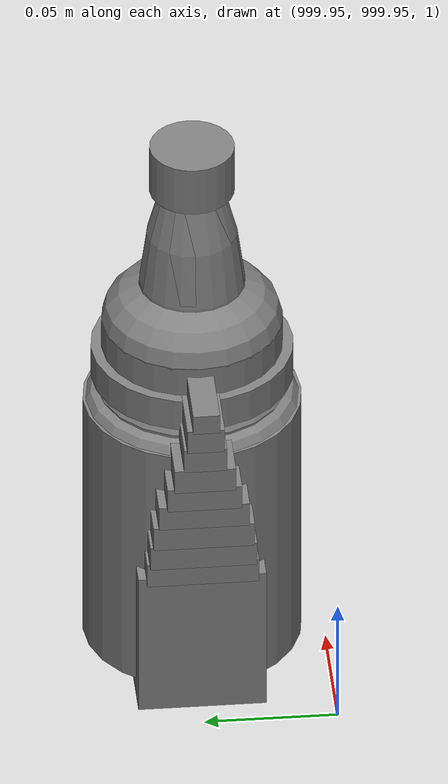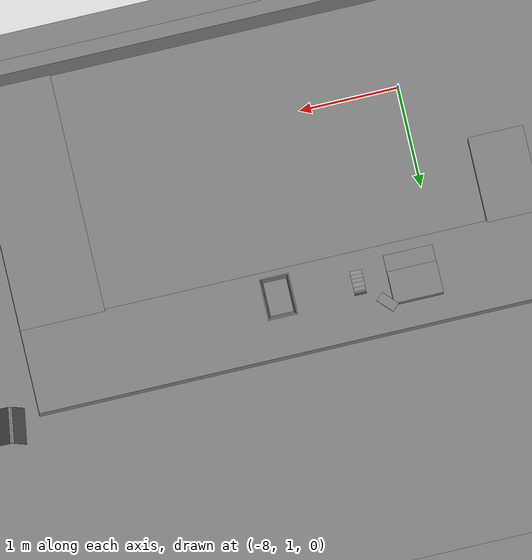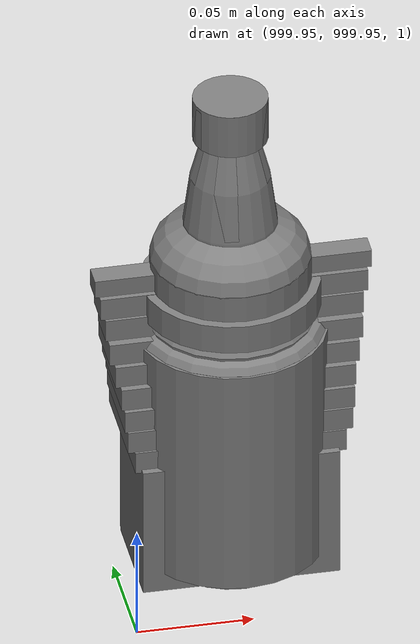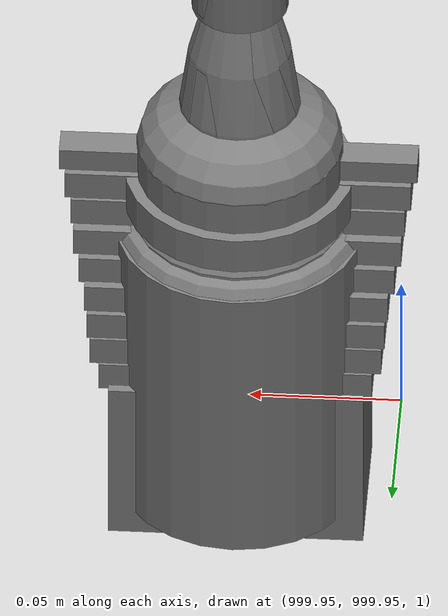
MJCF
<mujoco>
    <option gravity="0.000000000 0.000000000 -9.810000420" timestep="0.0166666" integrator="implicitfast" density="1.225" viscosity="1.8000001e-05" noslip_iterations="10" iterations="100" sdf_iterations="50">
        <flag multiccd="disable"/>
    </option>
    <size memory="1000M"/>
    <compiler coordinate="local"/>
    <worldbody>
        <light cutoff="30" pos="0 1 1" dir="0 -1 -2"/>
        <light cutoff="30" pos="0 -1 1" dir="0 1 -2"/>
        <body pos="0.000000000 0.000000000 0.000000000" euler="0.000000000 0.000000000 0.000000000" name=" Static Objects_ Static Objects">
            <geom contype="1" conaffinity="1" density="1000" type="box" material="" rgba="0.500000000 0.500000000 0.500000000 1.000000000" solimp="0.899999976 0.949999988 0.001000000" friction="1.000000000 0.005000000 0.000100000" solref="0.020000000 1.000000000" margin="0" condim="3" group="0" pos="-3.101639986 6.150595188 1.018643856" quat="1.000000000 0.000000000 0.000000000 0.000000000" size="0.050000001 0.579999983 1.019999981" name=" Static Objects_geom_AA34DF98_9753_415A_B9A4_CD092B55EC2B"/>
            <geom contype="1" conaffinity="1" density="1000" type="box" material="" rgba="0.500000000 0.500000000 0.500000000 1.000000000" solimp="0.899999976 0.949999988 0.001000000" friction="1.000000000 0.005000000 0.000100000" solref="0.020000000 1.000000000" margin="0" condim="3" group="0" pos="-2.825197220 6.153595448 1.115278244" quat="0.707107067 0.000000000 0.000000000 0.707106471" size="0.550000012 0.239999995 0.025000000" name=" Static Objects_geom_6E08F13E_71F8_4E8D_B0C9_FC0FEE53DEDF"/>
            <geom contype="1" conaffinity="1" density="1000" type="box" material="" rgba="0.500000000 0.500000000 0.500000000 1.000000000" solimp="0.899999976 0.949999988 0.001000000" friction="1.000000000 0.005000000 0.000100000" solref="0.020000000 1.000000000" margin="0" condim="3" group="0" pos="-2.825197220 6.153595448 0.097434282" quat="0.707107067 0.000000000 0.000000000 0.707106471" size="0.550000012 0.239999995 0.098999999" name=" Static Objects_geom_C13521A3_1AFC_44C4_BE8D_70ADAB969A1A"/>
            <geom contype="1" conaffinity="1" density="1000" type="box" material="" rgba="0.500000000 0.500000000 0.500000000 1.000000000" solimp="0.899999976 0.949999988 0.001000000" friction="1.000000000 0.005000000 0.000100000" solref="0.020000000 1.000000000" margin="0" condim="3" group="0" pos="-6.293097973 6.153595448 1.114443064" quat="0.707107067 0.000000000 0.000000000 0.707106471" size="0.529999971 3.134999990 0.025000000" name=" Static Objects_geom_FF05BF0E_D6B2_4543_8B1F_BEF3D82C6F35"/>
            <geom contype="1" conaffinity="1" density="1000" type="box" material="" rgba="0.500000000 0.500000000 0.500000000 1.000000000" solimp="0.899999976 0.949999988 0.001000000" friction="1.000000000 0.005000000 0.000100000" solref="0.020000000 1.000000000" margin="0" condim="3" group="0" pos="-2.825197220 6.153595448 1.563861728" quat="0.707107067 0.000000000 0.000000000 0.707106471" size="0.550000012 0.239999995 0.025000000" name=" Static Objects_geom_724DE584_0C3B_44B1_ADB3_8462963D11FB"/>
            <geom contype="1" conaffinity="1" density="1000" type="box" material="" rgba="0.500000000 0.500000000 0.500000000 1.000000000" solimp="0.899999976 0.949999988 0.001000000" friction="1.000000000 0.005000000 0.000100000" solref="0.020000000 1.000000000" margin="0" condim="3" group="0" pos="-6.311686516 6.153595448 1.018643856" quat="0.707107067 0.000000000 0.000000000 0.707106471" size="0.050000001 3.150000095 1.019999981" name=" Static Objects_geom_878B378E_88C2_4020_9FE1_006BF697F63B"/>
            <geom contype="1" conaffinity="1" density="1000" type="box" material="" rgba="0.500000000 0.500000000 0.500000000 1.000000000" solimp="0.899999976 0.949999988 0.001000000" friction="1.000000000 0.005000000 0.000100000" solref="0.020000000 1.000000000" margin="0" condim="3" group="0" pos="-6.286010742 6.153595448 0.096129179" quat="0.707107067 0.000000000 0.000000000 0.707106471" size="0.529999971 3.134999990 0.098999999" name=" Static Objects_geom_3765BB96_06F3_4221_85CC_B5AEF6BB6E07"/>
            <geom contype="1" conaffinity="1" density="1000" type="box" material="" rgba="0.500000000 0.500000000 0.500000000 1.000000000" solimp="0.899999976 0.949999988 0.001000000" friction="1.000000000 0.005000000 0.000100000" solref="0.020000000 1.000000000" margin="0" condim="3" group="0" pos="-2.825197220 6.153595448 0.629031777" quat="0.707107067 0.000000000 0.000000000 0.707106471" size="0.550000012 0.239999995 0.025000000" name=" Static Objects_geom_6EC6A32A_D5BE_47D6_9B46_AE00323713FC"/>
            <geom contype="1" conaffinity="1" density="1000" type="box" material="" rgba="0.500000000 0.500000000 0.500000000 1.000000000" solimp="0.899999976 0.949999988 0.001000000" friction="1.000000000 0.005000000 0.000100000" solref="0.020000000 1.000000000" margin="0" condim="3" group="0" pos="-6.286010742 6.153595448 1.563861728" quat="0.707107067 0.000000000 0.000000000 0.707106471" size="0.529999971 3.134999990 0.025000000" name=" Static Objects_geom_8D2B1D29_A8CD_410D_B6E6_695E391C5524"/>
            <geom contype="1" conaffinity="1" density="1000" type="box" material="" rgba="0.500000000 0.500000000 0.500000000 1.000000000" solimp="0.899999976 0.949999988 0.001000000" friction="1.000000000 0.005000000 0.000100000" solref="0.020000000 1.000000000" margin="0" condim="3" group="0" pos="-6.286010742 6.153595448 0.629031777" quat="0.707107067 0.000000000 0.000000000 0.707106471" size="0.529999971 3.134999990 0.025000000" name=" Static Objects_geom_D416FB89_30D5_4A98_9C2B_D14ACD002F38"/>
            <geom contype="1" conaffinity="1" density="1000" type="box" material="" rgba="0.500000000 0.500000000 0.500000000 1.000000000" solimp="0.899999976 0.949999988 0.001000000" friction="1.000000000 0.005000000 0.000100000" solref="0.020000000 1.000000000" margin="0" condim="3" group="0" pos="-7.719123363 2.867671013 1.173410416" quat="1.000000000 0.000000000 0.000000000 0.000000000" size="0.250000000 0.250000000 0.079999998" name=" Static Objects_geom_DFA212B6_FB83_40F6_97F5_7AAC1FDB7323"/>
            <geom contype="1" conaffinity="1" density="1000" type="box" material="" rgba="0.500000000 0.500000000 0.500000000 1.000000000" solimp="0.899999976 0.949999988 0.001000000" friction="1.000000000 0.005000000 0.000100000" solref="0.020000000 1.000000000" margin="0" condim="3" group="0" pos="-7.408766270 3.088089943 1.776644945" quat="0.928051054 0.000000000 0.000000000 0.372453064" size="0.050000001 0.100000001 0.050000001" name=" Static Objects_geom_B3A51009_3D0E_48D2_9382_5E1B4560FEDA"/>
            <geom contype="1" conaffinity="1" density="1000" type="box" material="" rgba="0.500000000 0.500000000 0.500000000 1.000000000" solimp="0.899999976 0.949999988 0.001000000" friction="1.000000000 0.005000000 0.000100000" solref="0.020000000 1.000000000" margin="0" condim="3" group="0" pos="-7.719123363 2.958004713 1.530241251" quat="1.000000000 0.000000000 0.000000000 0.000000000" size="0.250000000 0.159999996 0.280000001" name=" Static Objects_geom_09901142_B366_4FBB_8EF1_663815DD19E9"/>
            <geom contype="1" conaffinity="1" density="1000" type="cylinder" material="" rgba="0.500000000 0.500000000 0.500000000 1.000000000" solimp="0.899999976 0.949999988 0.001000000" friction="1.000000000 0.005000000 0.000100000" solref="0.020000000 1.000000000" margin="0" condim="3" group="0" pos="-7.427312374 3.069516420 1.502544641" quat="0.928051054 0.000000000 0.000000000 0.372453064" size="0.015000000 0.230000004 0.100000001" name=" Static Objects_geom_48FAF0AF_9BCD_4459_B88D_07BB256C5DB9"/>
            <geom contype="1" conaffinity="1" density="1000" type="box" material="" rgba="0.500000000 0.500000000 0.500000000 1.000000000" solimp="0.899999976 0.949999988 0.001000000" friction="1.000000000 0.005000000 0.000100000" solref="0.020000000 1.000000000" margin="0" condim="3" group="0" pos="-7.437745571 3.067511320 1.289965630" quat="1.000000000 0.000000000 0.000000000 0.000000000" size="0.029999999 0.020000000 0.020000000" name=" Static Objects_geom_83656409_7749_49B0_BBE0_72D0525F3DBB"/>
            <geom contype="1" conaffinity="1" density="1000" type="box" material="" rgba="0.500000000 0.500000000 0.500000000 1.000000000" solimp="0.899999976 0.949999988 0.001000000" friction="1.000000000 0.005000000 0.000100000" solref="0.020000000 1.000000000" margin="0" condim="3" group="0" pos="-9.058088303 6.434794426 1.209077358" quat="1.000000000 0.000000000 0.000000000 0.000000000" size="0.250000000 0.100000001 0.070000000" name=" Static Objects_geom_81E51AB7_42D4_4760_B522_3B96986C0295"/>
            <geom contype="1" conaffinity="1" density="1000" type="box" material="" rgba="0.500000000 0.500000000 0.500000000 1.000000000" solimp="0.899999976 0.949999988 0.001000000" friction="1.000000000 0.005000000 0.000100000" solref="0.020000000 1.000000000" margin="0" condim="3" group="0" pos="-7.886891365 6.459744930 0.352518857" quat="1.000000000 0.000000000 0.000000000 0.000000000" size="1.500000000 0.200000003 0.150000006" name=" Static Objects_geom_A6F53359_1CAA_4FEA_8CF2_40651BC4AD83"/>
            <geom contype="1" conaffinity="1" density="1000" type="box" material="" rgba="0.500000000 0.500000000 0.500000000 1.000000000" solimp="0.899999976 0.949999988 0.001000000" friction="1.000000000 0.005000000 0.000100000" solref="0.020000000 1.000000000" margin="0" condim="3" group="0" pos="-9.237723351 6.464855671 1.209077358" quat="1.000000000 0.000000000 0.000000000 0.000000000" size="0.100000001 0.100000001 0.070000000" name=" Static Objects_geom_C93804F6_7FBA_4E13_9F54_3C66D18029CF"/>
            <geom contype="1" conaffinity="1" density="1000" type="box" material="" rgba="0.500000000 0.500000000 0.500000000 1.000000000" solimp="0.899999976 0.949999988 0.001000000" friction="1.000000000 0.005000000 0.000100000" solref="0.020000000 1.000000000" margin="0" condim="3" group="0" pos="-6.924745083 6.362090111 1.214329123" quat="1.000000000 0.000000000 0.000000000 0.000000000" size="0.200000003 0.100000001 0.075000003" name=" Static Objects_geom_6DA5B551_2DA6_44A6_91A2_C7F073E2D69A"/>
            <geom contype="1" conaffinity="1" density="1000" type="box" material="" rgba="0.500000000 0.500000000 0.500000000 1.000000000" solimp="0.899999976 0.949999988 0.001000000" friction="1.000000000 0.005000000 0.000100000" solref="0.020000000 1.000000000" margin="0" condim="3" group="0" pos="-4.407354832 6.459744930 1.292199373" quat="1.000000000 0.000000000 0.000000000 0.000000000" size="1.240000010 0.200000003 0.150000006" name=" Static Objects_geom_5F584E61_58CA_471D_BA5C_F6114CD1F0C2"/>
            <geom contype="1" conaffinity="1" density="1000" type="box" material="" rgba="0.500000000 0.500000000 0.500000000 1.000000000" solimp="0.899999976 0.949999988 0.001000000" friction="1.000000000 0.005000000 0.000100000" solref="0.020000000 1.000000000" margin="0" condim="3" group="0" pos="-5.611940861 6.318420410 0.350975692" quat="1.000000000 0.000000000 0.000000000 0.000000000" size="0.699999988 0.100000001 0.150000006" name=" Static Objects_geom_A0197D29_3A7B_46EF_A794_BEBD8014BD78"/>
            <geom contype="1" conaffinity="1" density="1000" type="box" material="" rgba="0.500000000 0.500000000 0.500000000 1.000000000" solimp="0.899999976 0.949999988 0.001000000" friction="1.000000000 0.005000000 0.000100000" solref="0.020000000 1.000000000" margin="0" condim="3" group="0" pos="-6.300771236 6.459744930 1.744376063" quat="1.000000000 0.000000000 0.000000000 0.000000000" size="3.000000000 0.200000003 0.150000006" name=" Static Objects_geom_77BBD773_0062_42EA_AB44_45C39CFBAE6A"/>
            <geom contype="1" conaffinity="1" density="1000" type="box" material="" rgba="0.500000000 0.500000000 0.500000000 1.000000000" solimp="0.899999976 0.949999988 0.001000000" friction="1.000000000 0.005000000 0.000100000" solref="0.020000000 1.000000000" margin="0" condim="3" group="0" pos="-8.844120979 6.464855671 1.209077358" quat="1.000000000 0.000000000 0.000000000 0.000000000" size="0.100000001 0.100000001 0.070000000" name=" Static Objects_geom_047F28DF_E0DC_41BA_AD23_F2FC8130EB56"/>
            <geom contype="1" conaffinity="1" density="1000" type="box" material="" rgba="0.500000000 0.500000000 0.500000000 1.000000000" solimp="0.899999976 0.949999988 0.001000000" friction="1.000000000 0.005000000 0.000100000" solref="0.020000000 1.000000000" margin="0" condim="3" group="0" pos="-6.824534416 6.447464466 1.212718010" quat="1.000000000 0.000000000 0.000000000 0.000000000" size="0.100000001 0.100000001 0.075000003" name=" Static Objects_geom_E27F4ABD_41BB_4EB0_B6F0_1C1A8A3A9EF3"/>
            <geom contype="1" conaffinity="1" density="1000" type="box" material="" rgba="0.500000000 0.500000000 0.500000000 1.000000000" solimp="0.899999976 0.949999988 0.001000000" friction="1.000000000 0.005000000 0.000100000" solref="0.020000000 1.000000000" margin="0" condim="3" group="0" pos="-6.751636982 6.459744930 0.800981164" quat="1.000000000 0.000000000 0.000000000 0.000000000" size="2.200000048 0.200000003 0.150000006" name=" Static Objects_geom_7F562822_2C67_48D8_9B37_97BEF3CFC285"/>
            <geom contype="1" conaffinity="1" density="1000" type="box" material="" rgba="0.500000000 0.500000000 0.500000000 1.000000000" solimp="0.899999976 0.949999988 0.001000000" friction="1.000000000 0.005000000 0.000100000" solref="0.020000000 1.000000000" margin="0" condim="3" group="0" pos="-6.098561764 6.327973843 1.292199373" quat="1.000000000 0.000000000 0.000000000 0.000000000" size="0.500000000 0.100000001 0.150000006" name=" Static Objects_geom_5B710465_6AE9_470D_B5C8_B53FE7EBE2AA"/>
            <geom contype="1" conaffinity="1" density="1000" type="box" material="" rgba="0.500000000 0.500000000 0.500000000 1.000000000" solimp="0.899999976 0.949999988 0.001000000" friction="1.000000000 0.005000000 0.000100000" solref="0.020000000 1.000000000" margin="0" condim="3" group="0" pos="-3.907610416 6.318625927 0.800981164" quat="1.000000000 0.000000000 0.000000000 0.000000000" size="0.500000000 0.100000001 0.150000006" name=" Static Objects_geom_1F03644F_D760_463D_9BE4_CF4997E89AFC"/>
            <geom contype="1" conaffinity="1" density="1000" type="box" material="" rgba="0.500000000 0.500000000 0.500000000 1.000000000" solimp="0.899999976 0.949999988 0.001000000" friction="1.000000000 0.005000000 0.000100000" solref="0.020000000 1.000000000" margin="0" condim="3" group="0" pos="-7.373087406 6.458900928 1.214329123" quat="1.000000000 0.000000000 0.000000000 0.000000000" size="0.250000000 0.200000003 0.075000003" name=" Static Objects_geom_35AA1FA7_0D64_484A_9811_72EB583CBB3C"/>
            <geom contype="1" conaffinity="1" density="1000" type="box" material="" rgba="0.500000000 0.500000000 0.500000000 1.000000000" solimp="0.899999976 0.949999988 0.001000000" friction="1.000000000 0.005000000 0.000100000" solref="0.020000000 1.000000000" margin="0" condim="3" group="0" pos="-4.035642624 6.459744930 0.352518857" quat="1.000000000 0.000000000 0.000000000 0.000000000" size="0.800000012 0.200000003 0.150000006" name=" Static Objects_geom_D4CC1516_18EE_4C8B_98AC_BDEB70C1E491"/>
            <geom contype="1" conaffinity="1" density="1000" type="box" material="" rgba="0.500000000 0.500000000 0.500000000 1.000000000" solimp="0.899999976 0.949999988 0.001000000" friction="1.000000000 0.005000000 0.000100000" solref="0.020000000 1.000000000" margin="0" condim="3" group="0" pos="-6.460197449 2.937205315 0.548931718" quat="1.000000000 0.000000000 0.000000000 0.000000000" size="2.650000095 0.430000007 0.550000012" name=" Static Objects_geom_2A17AEDA_95B9_4C7B_ABA7_796D36785AD3"/>
            <geom contype="1" conaffinity="1" density="1000" type="box" material="" rgba="0.500000000 0.500000000 0.500000000 1.000000000" solimp="0.899999976 0.949999988 0.001000000" friction="1.000000000 0.005000000 0.000100000" solref="0.020000000 1.000000000" margin="0" condim="3" group="0" pos="-4.240264893 1.327049494 0.549888909" quat="1.000000000 0.000000000 0.000000000 0.000000000" size="0.430000007 1.200000048 0.550000012" name=" Static Objects_geom_CC414C16_F28A_42B9_A01A_FD9E63D448AA"/>
            <geom contype="1" conaffinity="1" density="1000" type="box" material="" rgba="0.500000000 0.500000000 0.500000000 1.000000000" solimp="0.899999976 0.949999988 0.001000000" friction="1.000000000 0.005000000 0.000100000" solref="0.020000000 1.000000000" margin="0" condim="3" group="0" pos="-8.830721855 2.096410990 0.549305558" quat="1.000000000 0.000000000 0.000000000 0.000000000" size="0.280000001 0.430000007 0.550000012" name=" Static Objects_geom_648ABF59_A6C3_48A7_8497_0FDC663F3A54"/>
            <geom contype="1" conaffinity="1" density="1000" type="plane" material="" rgba="0.500000000 0.500000000 0.500000000 1.000000000" solimp="0.899999976 0.949999988 0.001000000" friction="1.000000000 0.005000000 0.000100000" solref="0.020000000 1.000000000" margin="0" condim="3" group="0" pos="-6.000000000 10.399999619 0.000000000" quat="1.000000000 0.000000000 0.000000000 0.000000000" size="6.050000191 10.800000191 0.010000000" name=" Static Objects_geom_051AD9E6_7A36_445C_A779_445A579AB415"/>
            <geom contype="1" conaffinity="1" density="1000" type="box" material="" rgba="0.500000000 0.500000000 0.500000000 1.000000000" solimp="0.899999976 0.949999988 0.001000000" friction="1.000000000 0.005000000 0.000100000" solref="0.020000000 1.000000000" margin="0" condim="3" group="0" pos="-6.000000000 0.035000000 2.000000000" quat="1.000000000 0.000000000 0.000000000 0.000000000" size="6.079999924 0.070000000 2.000000000" name=" Static Objects_geom_BB487EB9_558F_4E5E_8977_97779590A6CF"/>
            <geom contype="1" conaffinity="1" density="1000" type="box" material="" rgba="0.500000000 0.500000000 0.500000000 1.000000000" solimp="0.899999976 0.949999988 0.001000000" friction="1.000000000 0.005000000 0.000100000" solref="0.020000000 1.000000000" margin="0" condim="3" group="0" pos="-6.000000000 20.159999847 2.000000000" quat="1.000000000 0.000000000 0.000000000 0.000000000" size="6.079999924 0.070000000 2.000000000" name=" Static Objects_geom_21B2037C_C775_4C97_B775_766EE03BF05A"/>
            <geom contype="1" conaffinity="1" density="1000" type="box" material="" rgba="0.500000000 0.500000000 0.500000000 1.000000000" solimp="0.899999976 0.949999988 0.001000000" friction="1.000000000 0.005000000 0.000100000" solref="0.020000000 1.000000000" margin="0" condim="3" group="0" pos="0.000000000 10.000000000 2.000000000" quat="1.000000000 0.000000000 0.000000000 0.000000000" size="0.070000000 10.500000000 2.000000000" name=" Static Objects_geom_08260A33_4A2C_459D_A09B_0D8D1E428624"/>
            <geom contype="1" conaffinity="1" density="1000" type="box" material="" rgba="0.500000000 0.500000000 0.500000000 1.000000000" solimp="0.899999976 0.949999988 0.001000000" friction="1.000000000 0.005000000 0.000100000" solref="0.020000000 1.000000000" margin="0" condim="3" group="0" pos="-12.050000191 10.000000000 2.000000000" quat="1.000000000 0.000000000 0.000000000 0.000000000" size="0.070000000 10.500000000 2.000000000" name=" Static Objects_geom_C8DB211F_762C_4D39_8A4F_6B5EA5341C23"/>
        </body>
        <body pos="-2.107308626 6.544377804 1.727304816" euler="-169.640884399 -27.863592148 70.943557739" mocap="true" name="spotlight3_SpotLight"/>
        <body pos="1000.000000000 1000.000000000 1.000000000" euler="0.000000000 0.000000000 0.000000000" name="openloong_gripper_2f85_fix_base_usda_bottle_red">
            <geom contype="1" conaffinity="1" density="1000" type="ellipsoid" material="" rgba="0.500000000 0.500000000 0.500000000 1.000000000" solimp="0.899999976 0.949999988 0.001000000" friction="1.000000000 0.005000000 0.000100000" solref="0.020000000 1.000000000" margin="0" condim="3" group="0" pos="0.000000000 0.000000000 0.144284487" quat="1.000000000 0.000000000 0.000000000 0.000000000" size="0.021000000 0.021000000 0.079999998" name="openloong_gripper_2f85_fix_base_usda_geom_E7BC0791_969A_46B0_BCB6_589066DBBE53"/>
            <geom contype="1" conaffinity="1" density="1000" type="cylinder" material="" rgba="0.500000000 0.500000000 0.500000000 1.000000000" solimp="0.899999976 0.949999988 0.001000000" friction="1.000000000 0.005000000 0.000100000" solref="0.020000000 1.000000000" margin="0" condim="3" group="0" pos="0.000000000 0.000000000 0.220618963" quat="1.000000000 0.000000000 0.000000000 0.000000000" size="0.016000001 0.010000000 1.000000000" name="openloong_gripper_2f85_fix_base_usda_geom_8F47CDD9_69A0_48A3_851D_22AD44FEF59C"/>
            <geom contype="1" conaffinity="1" density="1000" type="ellipsoid" material="" rgba="0.500000000 0.500000000 0.500000000 1.000000000" solimp="0.899999976 0.949999988 0.001000000" friction="1.000000000 0.005000000 0.000100000" solref="0.020000000 1.000000000" margin="0" condim="3" group="0" pos="0.000000000 0.000000000 0.118945479" quat="1.000000000 0.000000000 0.000000000 0.000000000" size="0.030999999 0.030999999 0.029999999" name="openloong_gripper_2f85_fix_base_usda_geom_F188E6A8_8279_43CD_9C0A_7146D5EE7180"/>
            <geom contype="1" conaffinity="1" density="1000" type="box" material="" rgba="0.500000000 0.500000000 0.500000000 1.000000000" solimp="0.899999976 0.949999988 0.001000000" friction="1.000000000 0.005000000 0.000100000" solref="0.020000000 1.000000000" margin="0" condim="3" group="0" pos="0.000000000 0.000000000 0.002189159" quat="1.000000000 0.000000000 0.000000000 0.000000000" size="0.020000000 0.020000000 0.003000000" name="openloong_gripper_2f85_fix_base_usda_geom_8685EA6B_2BEE_4D14_A945_C55D4F81FE9C"/>
            <geom contype="1" conaffinity="1" density="1000" type="cylinder" material="" rgba="0.500000000 0.500000000 0.500000000 1.000000000" solimp="0.899999976 0.949999988 0.001000000" friction="1.000000000 0.005000000 0.000100000" solref="0.020000000 1.000000000" margin="0" condim="3" group="0" pos="0.000000000 -0.000366211 0.060884237" quat="1.000000000 0.000000000 0.000000000 0.000000000" size="0.030999999 0.057999998 1.000000000" name="openloong_gripper_2f85_fix_base_usda_geom_C1DC36E1_53D0_49D8_A434_814FF5B7B56F"/>
            <freejoint name="openloong_gripper_2f85_fix_base_usda_bottle_red_joint"/>
            <site size="0.005000000 0.005000000 0.005000000" rgba="0.500000000 0.500000000 0.500000000 1.000000000" pos="0.000000000 0.000000000 0.000000000" quat="0.999961913 0.008726535 0.000000000 0.000000000" group="0" type="sphere" name="openloong_gripper_2f85_fix_base_usda_bottle_redsite"/>
        </body>
        <body pos="1000.000000000 1000.000000000 1.000000000" euler="0.000000000 0.000000000 0.000000000" name="openloong_gripper_2f85_fix_base_usda_can">
            <geom contype="1" conaffinity="1" density="1000" type="cylinder" material="" rgba="0.500000000 0.500000000 0.500000000 1.000000000" solimp="0.899999976 0.949999988 0.001000000" friction="1.000000000 0.005000000 0.000100000" solref="0.020000000 1.000000000" margin="0" condim="3" group="0" pos="0.000000000 0.000000000 0.079676986" quat="1.000000000 0.000000000 0.000000000 0.000000000" size="0.034000002 0.071999997 1.000000000" name="openloong_gripper_2f85_fix_base_usda_geom_CBD8849B_0093_465B_9FE7_F4C0A3794E9D"/>
            <geom contype="1" conaffinity="1" density="1000" type="ellipsoid" material="" rgba="0.500000000 0.500000000 0.500000000 1.000000000" solimp="0.899999976 0.949999988 0.001000000" friction="1.000000000 0.005000000 0.000100000" solref="0.020000000 1.000000000" margin="0" condim="3" group="0" pos="0.000000000 0.000000000 0.151854277" quat="1.000000000 0.000000000 0.000000000 0.000000000" size="0.034000002 0.034000002 0.020000000" name="openloong_gripper_2f85_fix_base_usda_geom_B3EA71DF_11F7_43D8_9ED3_0E500870D0E9"/>
            <geom contype="1" conaffinity="1" density="1000" type="box" material="" rgba="0.500000000 0.500000000 0.500000000 1.000000000" solimp="0.899999976 0.949999988 0.001000000" friction="1.000000000 0.005000000 0.000100000" solref="0.020000000 1.000000000" margin="0" condim="3" group="0" pos="0.000000000 0.000000000 0.004777670" quat="1.000000000 0.000000000 0.000000000 0.000000000" size="0.020000000 0.020000000 0.005000000" name="openloong_gripper_2f85_fix_base_usda_geom_4F31D154_A555_40B0_88B7_AC2B41EB7618"/>
            <freejoint name="openloong_gripper_2f85_fix_base_usda_can_joint"/>
            <site size="0.005000000 0.005000000 0.005000000" rgba="0.500000000 0.500000000 0.500000000 1.000000000" pos="0.000000000 0.000000000 0.000000000" quat="1.000000000 0.000000000 0.000000000 0.000000000" group="0" type="sphere" name="openloong_gripper_2f85_fix_base_usda_cansite"/>
        </body>
        <body pos="1000.000000000 1000.000000000 1.000000000" euler="0.000000000 0.000000000 0.000000000" name="openloong_gripper_2f85_fix_base_usda_jar_01">
            <geom contype="1" conaffinity="1" density="1000" type="box" material="" rgba="0.500000000 0.500000000 0.500000000 1.000000000" solimp="0.899999976 0.949999988 0.001000000" friction="1.000000000 0.005000000 0.000100000" solref="0.020000000 1.000000000" margin="0" condim="3" group="0" pos="0.000000000 0.000000000 0.006158113" quat="1.000000000 0.000000000 0.000000000 0.000000000" size="0.020000000 0.020000000 0.005000000" name="openloong_gripper_2f85_fix_base_usda_geom_EEA5E8F4_CA07_4FD1_B659_92EAA70E0161"/>
            <geom contype="1" conaffinity="1" density="1000" type="cylinder" material="" rgba="0.500000000 0.500000000 0.500000000 1.000000000" solimp="0.899999976 0.949999988 0.001000000" friction="1.000000000 0.005000000 0.000100000" solref="0.020000000 1.000000000" margin="0" condim="3" group="0" pos="0.000000000 0.000000000 0.062744498" quat="1.000000000 0.000000000 0.000000000 0.000000000" size="0.041000001 0.052999999 1.000000000" name="openloong_gripper_2f85_fix_base_usda_geom_AB631CE8_0E97_4970_9CCD_007A81741DBE"/>
            <geom contype="1" conaffinity="1" density="1000" type="ellipsoid" material="" rgba="0.500000000 0.500000000 0.500000000 1.000000000" solimp="0.899999976 0.949999988 0.001000000" friction="1.000000000 0.005000000 0.000100000" solref="0.020000000 1.000000000" margin="0" condim="3" group="0" pos="0.000000000 0.000000000 0.122252703" quat="1.000000000 0.000000000 0.000000000 0.000000000" size="0.035999998 0.035999998 0.010000000" name="openloong_gripper_2f85_fix_base_usda_geom_552902BA_2504_4C08_B414_B93143E2053A"/>
            <geom contype="1" conaffinity="1" density="1000" type="cylinder" material="" rgba="0.500000000 0.500000000 0.500000000 1.000000000" solimp="0.899999976 0.949999988 0.001000000" friction="1.000000000 0.005000000 0.000100000" solref="0.020000000 1.000000000" margin="0" condim="3" group="0" pos="0.000000000 0.000000000 0.015747190" quat="1.000000000 0.000000000 0.000000000 0.000000000" size="0.035000000 0.010000000 1.000000000" name="openloong_gripper_2f85_fix_base_usda_geom_279B0687_F7E6_47F6_9DD3_8CBA3D62CF49"/>
            <geom contype="1" conaffinity="1" density="1000" type="ellipsoid" material="" rgba="0.500000000 0.500000000 0.500000000 1.000000000" solimp="0.899999976 0.949999988 0.001000000" friction="1.000000000 0.005000000 0.000100000" solref="0.020000000 1.000000000" margin="0" condim="3" group="0" pos="0.000000000 0.000000000 0.115815401" quat="1.000000000 0.000000000 0.000000000 0.000000000" size="0.039999999 0.039999999 0.010000000" name="openloong_gripper_2f85_fix_base_usda_geom_F02717EB_314C_4FE3_B521_EA00983014F2"/>
            <geom contype="1" conaffinity="1" density="1000" type="cylinder" material="" rgba="0.500000000 0.500000000 0.500000000 1.000000000" solimp="0.899999976 0.949999988 0.001000000" friction="1.000000000 0.005000000 0.000100000" solref="0.020000000 1.000000000" margin="0" condim="3" group="0" pos="0.000000000 0.000000000 0.133183479" quat="1.000000000 0.000000000 0.000000000 0.000000000" size="0.037999999 0.006500000 1.000000000" name="openloong_gripper_2f85_fix_base_usda_geom_1D5FD352_EB73_4F3D_BE72_DDA617566A5E"/>
            <freejoint name="openloong_gripper_2f85_fix_base_usda_jar_01_joint"/>
            <site size="0.005000000 0.005000000 0.005000000" rgba="0.500000000 0.500000000 0.500000000 1.000000000" pos="0.000000000 0.000000000 0.000000000" quat="1.000000000 0.000000000 0.000000000 0.000000000" group="0" type="sphere" name="openloong_gripper_2f85_fix_base_usda_jar_01site"/>
        </body>
        <body pos="1000.000000000 1000.000000000 1.000000000" euler="0.000000000 0.000000000 0.000000000" name="openloong_gripper_2f85_fix_base_usda_bottle_blue">
            <geom contype="1" conaffinity="1" density="1000" type="ellipsoid" material="" rgba="0.500000000 0.500000000 0.500000000 1.000000000" solimp="0.899999976 0.949999988 0.001000000" friction="1.000000000 0.005000000 0.000100000" solref="0.020000000 1.000000000" margin="0" condim="3" group="0" pos="0.000000000 0.000000000 0.118920922" quat="1.000000000 0.000000000 0.000000000 0.000000000" size="0.030999999 0.030999999 0.029999999" name="openloong_gripper_2f85_fix_base_usda_geom_AA5AA115_D97F_46F8_8384_15800CC56613"/>
            <geom contype="1" conaffinity="1" density="1000" type="box" material="" rgba="0.500000000 0.500000000 0.500000000 1.000000000" solimp="0.899999976 0.949999988 0.001000000" friction="1.000000000 0.005000000 0.000100000" solref="0.020000000 1.000000000" margin="0" condim="3" group="0" pos="0.000000000 0.000000000 0.002164602" quat="1.000000000 0.000000000 0.000000000 0.000000000" size="0.020000000 0.020000000 0.003000000" name="openloong_gripper_2f85_fix_base_usda_geom_8CDED359_9BDE_47CF_8648_25D66AE830C9"/>
            <geom contype="1" conaffinity="1" density="1000" type="cylinder" material="" rgba="0.500000000 0.500000000 0.500000000 1.000000000" solimp="0.899999976 0.949999988 0.001000000" friction="1.000000000 0.005000000 0.000100000" solref="0.020000000 1.000000000" margin="0" condim="3" group="0" pos="0.000000000 -0.000366211 0.060859680" quat="1.000000000 0.000000000 0.000000000 0.000000000" size="0.030999999 0.057999998 1.000000000" name="openloong_gripper_2f85_fix_base_usda_geom_E45D0006_E4D4_41E7_8F38_17DDA51419C7"/>
            <geom contype="1" conaffinity="1" density="1000" type="cylinder" material="" rgba="0.500000000 0.500000000 0.500000000 1.000000000" solimp="0.899999976 0.949999988 0.001000000" friction="1.000000000 0.005000000 0.000100000" solref="0.020000000 1.000000000" margin="0" condim="3" group="0" pos="0.000000000 0.000000000 0.220594406" quat="1.000000000 0.000000000 0.000000000 0.000000000" size="0.016000001 0.010000000 1.000000000" name="openloong_gripper_2f85_fix_base_usda_geom_76374291_7F1E_435E_9914_B1978C97053A"/>
            <geom contype="1" conaffinity="1" density="1000" type="ellipsoid" material="" rgba="0.500000000 0.500000000 0.500000000 1.000000000" solimp="0.899999976 0.949999988 0.001000000" friction="1.000000000 0.005000000 0.000100000" solref="0.020000000 1.000000000" margin="0" condim="3" group="0" pos="0.000000000 0.000000000 0.144259930" quat="1.000000000 0.000000000 0.000000000 0.000000000" size="0.021000000 0.021000000 0.079999998" name="openloong_gripper_2f85_fix_base_usda_geom_4D045DC5_13A9_46A4_9FE4_83E637FDB9C2"/>
            <freejoint name="openloong_gripper_2f85_fix_base_usda_bottle_blue_joint"/>
            <site size="0.005000000 0.005000000 0.005000000" rgba="0.500000000 0.500000000 0.500000000 1.000000000" pos="0.000000000 0.000000000 0.000000000" quat="0.999961913 0.008726535 0.000000000 0.000000000" group="0" type="sphere" name="openloong_gripper_2f85_fix_base_usda_bottle_bluesite"/>
        </body>
        <body pos="-1.765674233 6.608308792 1.765635729" euler="75.022727966 -8.612553596 111.261497498" mocap="true" name="spotlight2_SpotLight"/>
        <body pos="1000.000000000 1000.000000000 1.000000000" euler="0.000000000 0.000000000 0.000000000" name="openloong_gripper_2f85_fix_base_usda_salt">
            <geom contype="1" conaffinity="1" density="1000" type="box" material="" rgba="0.500000000 0.500000000 0.500000000 1.000000000" solimp="0.899999976 0.949999988 0.001000000" friction="1.000000000 0.005000000 0.000100000" solref="0.020000000 1.000000000" margin="0" condim="3" group="0" pos="0.000305176 0.000000000 0.084862232" quat="1.000000000 0.000000000 0.000000000 0.000000000" size="0.048999999 0.018999999 0.005000000" name="openloong_gripper_2f85_fix_base_usda_geom_4347DF60_82D4_4DE8_A4CB_0576F884B954"/>
            <geom contype="1" conaffinity="1" density="1000" type="box" material="" rgba="0.500000000 0.500000000 0.500000000 1.000000000" solimp="0.899999976 0.949999988 0.001000000" friction="1.000000000 0.005000000 0.000100000" solref="0.020000000 1.000000000" margin="0" condim="3" group="0" pos="0.000305176 0.000000000 0.104564309" quat="1.000000000 0.000000000 0.000000000 0.000000000" size="0.052000001 0.014000000 0.005000000" name="openloong_gripper_2f85_fix_base_usda_geom_BC0AD395_E27D_4D31_861E_FC08B3A5037E"/>
            <geom contype="1" conaffinity="1" density="1000" type="box" material="" rgba="0.500000000 0.500000000 0.500000000 1.000000000" solimp="0.899999976 0.949999988 0.001000000" friction="1.000000000 0.005000000 0.000100000" solref="0.020000000 1.000000000" margin="0" condim="3" group="0" pos="0.000305176 0.000000000 0.114487171" quat="1.000000000 0.000000000 0.000000000 0.000000000" size="0.054000001 0.011500000 0.005000000" name="openloong_gripper_2f85_fix_base_usda_geom_321C5986_A609_4DCC_B16C_6CC18786CA9E"/>
            <geom contype="1" conaffinity="1" density="1000" type="box" material="" rgba="0.500000000 0.500000000 0.500000000 1.000000000" solimp="0.899999976 0.949999988 0.001000000" friction="1.000000000 0.005000000 0.000100000" solref="0.020000000 1.000000000" margin="0" condim="3" group="0" pos="0.000305176 0.000000000 0.075103164" quat="1.000000000 0.000000000 0.000000000 0.000000000" size="0.048000000 0.020000000 0.005000000" name="openloong_gripper_2f85_fix_base_usda_geom_648AC6CE_8EA7_4D8A_9279_1A4B502ADCFA"/>
            <geom contype="1" conaffinity="1" density="1000" type="box" material="" rgba="0.500000000 0.500000000 0.500000000 1.000000000" solimp="0.899999976 0.949999988 0.001000000" friction="1.000000000 0.005000000 0.000100000" solref="0.020000000 1.000000000" margin="0" condim="3" group="0" pos="0.000305176 0.000000000 0.134892464" quat="1.000000000 0.000000000 0.000000000 0.000000000" size="0.057000000 0.007000000 0.005000000" name="openloong_gripper_2f85_fix_base_usda_geom_44BFD3CE_F813_4131_A181_E68EB24B82E9"/>
            <geom contype="1" conaffinity="1" density="1000" type="box" material="" rgba="0.500000000 0.500000000 0.500000000 1.000000000" solimp="0.899999976 0.949999988 0.001000000" friction="1.000000000 0.005000000 0.000100000" solref="0.020000000 1.000000000" margin="0" condim="3" group="0" pos="0.000305176 0.000000000 0.094920278" quat="1.000000000 0.000000000 0.000000000 0.000000000" size="0.050000001 0.017000001 0.005000000" name="openloong_gripper_2f85_fix_base_usda_geom_C3B4340B_398F_4E5A_8138_A8F76D0AEDD4"/>
            <geom contype="1" conaffinity="1" density="1000" type="box" material="" rgba="0.500000000 0.500000000 0.500000000 1.000000000" solimp="0.899999976 0.949999988 0.001000000" friction="1.000000000 0.005000000 0.000100000" solref="0.020000000 1.000000000" margin="0" condim="3" group="0" pos="0.000305176 0.000000000 0.065204859" quat="1.000000000 0.000000000 0.000000000 0.000000000" size="0.045000002 0.021000000 0.005000000" name="openloong_gripper_2f85_fix_base_usda_geom_DC554894_0762_40E3_962E_347F85539F28"/>
            <geom contype="1" conaffinity="1" density="1000" type="box" material="" rgba="0.500000000 0.500000000 0.500000000 1.000000000" solimp="0.899999976 0.949999988 0.001000000" friction="1.000000000 0.005000000 0.000100000" solref="0.020000000 1.000000000" margin="0" condim="3" group="0" pos="0.000305176 0.000000000 0.144135714" quat="1.000000000 0.000000000 0.000000000 0.000000000" size="0.059000000 0.005000000 0.004000000" name="openloong_gripper_2f85_fix_base_usda_geom_34B3CCCA_A6B8_46C5_981D_FA664E379E43"/>
            <geom contype="1" conaffinity="1" density="1000" type="box" material="" rgba="0.500000000 0.500000000 0.500000000 1.000000000" solimp="0.899999976 0.949999988 0.001000000" friction="1.000000000 0.005000000 0.000100000" solref="0.020000000 1.000000000" margin="0" condim="3" group="0" pos="0.000000000 0.000000000 0.031593561" quat="1.000000000 0.000000000 0.000000000 0.000000000" size="0.041999999 0.024000000 0.029999999" name="openloong_gripper_2f85_fix_base_usda_geom_AAE4B61A_29D3_4528_A524_77F51FC6D255"/>
            <geom contype="1" conaffinity="1" density="1000" type="box" material="" rgba="0.500000000 0.500000000 0.500000000 1.000000000" solimp="0.899999976 0.949999988 0.001000000" friction="1.000000000 0.005000000 0.000100000" solref="0.020000000 1.000000000" margin="0" condim="3" group="0" pos="0.000305176 0.000000000 0.124608755" quat="1.000000000 0.000000000 0.000000000 0.000000000" size="0.055000000 0.008000000 0.005000000" name="openloong_gripper_2f85_fix_base_usda_geom_3508BE25_DA4B_4C2F_A5C2_7760C3DF9586"/>
            <freejoint name="openloong_gripper_2f85_fix_base_usda_salt_joint"/>
            <site size="0.005000000 0.005000000 0.005000000" rgba="0.500000000 0.500000000 0.500000000 1.000000000" pos="0.000000000 0.000000000 0.000000000" quat="1.000000000 0.000000000 0.000000000 0.000000000" group="0" type="sphere" name="openloong_gripper_2f85_fix_base_usda_saltsite"/>
        </body>
        <body pos="-2.267348051 6.444875717 1.754498720" euler="41.373851776 81.511390686 -161.509658813" mocap="true" name="spotlight6_SpotLight"/>
        <body pos="0.000000000 0.000000000 0.000000000" euler="0.000000000 0.000000000 0.000000000" name="Interactive Objects_Interactive Objects"/>
        <body pos="-3.510578632 3.403555870 -0.000000100" euler="0.000000000 0.000000000 40.200675964" name="openloong_gripper_2f85_fix_base_usda_PZ">
            <geom contype="1" conaffinity="1" density="1000" type="box" material="" rgba="0.500000000 0.500000000 0.500000000 1.000000000" solimp="0.899999976 0.949999988 0.001000000" friction="1.000000000 0.005000000 0.000100000" solref="0.020000000 1.000000000" margin="0" condim="3" group="0" pos="-0.047453165 0.056484699 0.373715430" quat="0.934750080 0.077914521 0.028795123 0.345459938" size="0.180000007 0.010000000 0.379999995" name="openloong_gripper_2f85_fix_base_usda_geom_0CDBC562_0E15_457C_BD96_1D78981E9715"/>
            <geom contype="1" conaffinity="1" density="1000" type="box" material="" rgba="0.500000000 0.500000000 0.500000000 1.000000000" solimp="0.899999976 0.949999988 0.001000000" friction="1.000000000 0.005000000 0.000100000" solref="0.020000000 1.000000000" margin="0" condim="3" group="0" pos="0.047452450 -0.054376602 0.374072611" quat="0.934387863 -0.082143910 -0.030358355 0.345326364" size="0.180000007 0.010000000 0.379999995" name="openloong_gripper_2f85_fix_base_usda_geom_8807E966_8616_46FD_82EB_8C566AE91BF5"/>
            <freejoint name="openloong_gripper_2f85_fix_base_usda_PZ"/>
        </body>
        <body pos="-6.332345009 2.779978037 1.034067392" euler="0.000000000 0.000000000 0.000000000" name="openloong_gripper_2f85_fix_base_usda_basket">
            <geom contype="1" conaffinity="1" density="100000" type="box" material="" rgba="0.500000000 0.500000000 0.500000000 1.000000000" solimp="0.899999976 0.949999988 0.001000000" friction="1.000000000 0.899999976 0.000100000" solref="0.020000000 1.000000000" margin="0" condim="3" group="0" pos="-0.172339439 0.000000000 0.168361664" quat="0.706172407 -0.036353018 -0.036353093 0.706170976" size="0.200000003 0.006000000 0.108000003" name="openloong_gripper_2f85_fix_base_usda_geom_3816E9C7_6CB8_4187_8F44_EA30E5C14582"/>
            <geom contype="1" conaffinity="1" density="100000" type="box" material="" rgba="0.500000000 0.500000000 0.500000000 1.000000000" solimp="0.899999976 0.949999988 0.001000000" friction="1.000000000 0.899999976 0.000100000" solref="0.020000000 1.000000000" margin="0" condim="3" group="0" pos="-0.039724827 -0.188568115 0.167089701" quat="0.997537494 0.070135131 0.000000000 0.000000000" size="0.150000006 0.006000000 0.108000003" name="openloong_gripper_2f85_fix_base_usda_geom_14F9B89A_22B4_4C8A_83C2_E0B265669510"/>
            <geom contype="1" conaffinity="1" density="100000" type="box" material="" rgba="0.500000000 0.500000000 0.500000000 1.000000000" solimp="0.899999976 0.949999988 0.001000000" friction="1.000000000 0.899999976 0.000100000" solref="0.020000000 1.000000000" margin="0" condim="3" group="0" pos="-0.039724827 0.188377380 0.167089701" quat="0.997489929 -0.070808925 0.000000000 0.000000000" size="0.150000006 0.006000000 0.108000003" name="openloong_gripper_2f85_fix_base_usda_geom_4A1C9A50_9D04_47B2_B317_AB1BD01D2189"/>
            <geom contype="1" conaffinity="1" density="100000" type="box" material="" rgba="0.500000000 0.500000000 0.500000000 1.000000000" solimp="0.899999976 0.949999988 0.001000000" friction="1.000000000 0.899999976 0.000100000" solref="0.020000000 1.000000000" margin="0" condim="3" group="0" pos="-0.039724827 0.000000000 0.068126202" quat="1.000000000 0.000000000 0.000000000 0.000000000" size="0.129999995 0.174999997 0.006000000" name="openloong_gripper_2f85_fix_base_usda_geom_45B27A5E_9FE2_496A_848D_EDFBD7CF440F"/>
            <geom contype="1" conaffinity="1" density="100000" type="box" material="" rgba="0.500000000 0.500000000 0.500000000 1.000000000" solimp="0.899999976 0.949999988 0.001000000" friction="1.000000000 0.899999976 0.000100000" solref="0.020000000 1.000000000" margin="0" condim="3" group="0" pos="0.094372749 0.000000000 0.168361664" quat="0.706172049 0.036353335 0.036353379 0.706171215" size="0.200000003 0.006000000 0.108000003" name="openloong_gripper_2f85_fix_base_usda_geom_651005E0_5A1B_413B_8BF3_5F62C73D1A45"/>
            <freejoint name="openloong_gripper_2f85_fix_base_usda_basket_joint"/>
            <site size="0.005000000 0.005000000 0.005000000" rgba="0.500000000 0.500000000 0.500000000 1.000000000" pos="0.000000000 0.000000000 0.000000000" quat="1.000000000 0.000000000 0.000000000 0.000000000" group="0" type="sphere" name="openloong_gripper_2f85_fix_base_usda_basketsite"/>
        </body>
        <body pos="-7.168000221 2.823999882 1.227496982" euler="-0.283413976 0.056829724 -0.133293271" name="openloong_gripper_2f85_fix_base_usda_Pos">
            <geom contype="1" conaffinity="1" density="1000" type="box" material="" rgba="0.500000000 0.500000000 0.500000000 1.000000000" solimp="0.899999976 0.949999988 0.001000000" friction="1.000000000 0.005000000 0.000100000" solref="0.020000000 1.000000000" margin="0" condim="3" group="0" pos="-0.002278805 0.074524641 -0.004134059" quat="0.315989345 0.948763072 -0.000000000 0.000000000" size="0.059999999 0.013000000 0.035000000" name="openloong_gripper_2f85_fix_base_usda_geom_E39D77A9_79AE_4AC6_B11B_1C920C43DF9E"/>
            <geom contype="1" conaffinity="1" density="1000" type="box" material="" rgba="0.500000000 0.500000000 0.500000000 1.000000000" solimp="0.899999976 0.949999988 0.001000000" friction="1.000000000 0.005000000 0.000100000" solref="0.020000000 1.000000000" margin="0" condim="3" group="0" pos="-0.002278805 0.078031301 0.008128285" quat="0.990447521 -0.137893379 -0.000000000 -0.000000000" size="0.059999999 0.010000000 0.035000000" name="openloong_gripper_2f85_fix_base_usda_geom_A922C740_8B09_4ED7_B76D_3697AAC6F277"/>
            <geom contype="1" conaffinity="1" density="1000" type="box" material="" rgba="0.500000000 0.500000000 0.500000000 1.000000000" solimp="0.899999976 0.949999988 0.001000000" friction="1.000000000 0.005000000 0.000100000" solref="0.020000000 1.000000000" margin="0" condim="3" group="0" pos="-0.002278805 0.080785275 -0.002596974" quat="0.287325472 -0.957833409 0.000000000 -0.000000000" size="0.059999999 0.013000000 0.035000000" name="openloong_gripper_2f85_fix_base_usda_geom_668F290E_70E3_409D_AE48_5E86C85A7B35"/>
            <geom contype="1" conaffinity="1" density="1000" type="box" material="" rgba="0.500000000 0.500000000 0.500000000 1.000000000" solimp="0.899999976 0.949999988 0.001000000" friction="1.000000000 0.005000000 0.000100000" solref="0.020000000 1.000000000" margin="0" condim="3" group="0" pos="-0.002278805 -0.098804474 -0.020146966" quat="0.988851666 0.148906454 0.000000000 -0.000000000" size="0.059999999 0.022000000 0.020000000" name="openloong_gripper_2f85_fix_base_usda_geom_91FF3771_1CC7_4895_93A8_8954CA9DB98F"/>
            <geom contype="1" conaffinity="1" density="1000" type="box" material="" rgba="0.500000000 0.500000000 0.500000000 1.000000000" solimp="0.899999976 0.949999988 0.001000000" friction="1.000000000 0.005000000 0.000100000" solref="0.020000000 1.000000000" margin="0" condim="3" group="0" pos="-0.002279282 0.019920111 0.012102962" quat="0.995421767 0.095583342 -0.000000000 -0.000000000" size="0.059999999 0.025000000 0.026000001" name="openloong_gripper_2f85_fix_base_usda_geom_926E47BF_4315_4BDD_A403_DD61EB768192"/>
            <geom contype="1" conaffinity="1" density="1000" type="box" material="" rgba="0.500000000 0.500000000 0.500000000 1.000000000" solimp="0.899999976 0.949999988 0.001000000" friction="1.000000000 0.005000000 0.000100000" solref="0.020000000 1.000000000" margin="0" condim="3" group="0" pos="-0.002279282 0.005734444 -0.014276862" quat="0.999571741 -0.029275302 -0.000000000 -0.000000000" size="0.059999999 0.050000001 0.010000000" name="openloong_gripper_2f85_fix_base_usda_geom_F9F9AC57_EE46_4224_88BB_56F363E78435"/>
            <geom contype="1" conaffinity="1" density="1000" type="box" material="" rgba="0.500000000 0.500000000 0.500000000 1.000000000" solimp="0.899999976 0.949999988 0.001000000" friction="1.000000000 0.005000000 0.000100000" solref="0.020000000 1.000000000" margin="0" condim="3" group="0" pos="-0.002278805 0.079460382 0.007771969" quat="0.922590554 -0.385781586 0.000000000 -0.000000000" size="0.059999999 0.010000000 0.035000000" name="openloong_gripper_2f85_fix_base_usda_geom_40E56B6E_85AE_4871_A088_773EEFBE047B"/>
            <geom contype="1" conaffinity="1" density="1000" type="box" material="" rgba="0.500000000 0.500000000 0.500000000 1.000000000" solimp="0.899999976 0.949999988 0.001000000" friction="1.000000000 0.005000000 0.000100000" solref="0.020000000 1.000000000" margin="0" condim="3" group="0" pos="-0.002279282 0.081384182 -0.001320124" quat="0.590483785 -0.807049930 0.000000000 -0.000000000" size="0.059999999 0.013000000 0.035000000" name="openloong_gripper_2f85_fix_base_usda_geom_39BE2E2A_AF34_43A9_9D93_CCFE64A16FC8"/>
            <geom contype="1" conaffinity="1" density="1000" type="box" material="" rgba="0.500000000 0.500000000 0.500000000 1.000000000" solimp="0.899999976 0.949999988 0.001000000" friction="1.000000000 0.005000000 0.000100000" solref="0.020000000 1.000000000" margin="0" condim="3" group="0" pos="-0.002278805 -0.059297800 -0.007972836" quat="0.988851666 0.148906454 0.000000000 -0.000000000" size="0.059999999 0.020000000 0.022000000" name="openloong_gripper_2f85_fix_base_usda_geom_F8D616C8_916E_4610_9C9B_2A8692A369CA"/>
            <geom contype="1" conaffinity="1" density="1000" type="box" material="" rgba="0.500000000 0.500000000 0.500000000 1.000000000" solimp="0.899999976 0.949999988 0.001000000" friction="1.000000000 0.005000000 0.000100000" solref="0.020000000 1.000000000" margin="0" condim="3" group="0" pos="-0.002278805 0.076618671 -0.004656792" quat="0.004634961 0.999989629 -0.000000000 0.000000000" size="0.059999999 0.013000000 0.035000000" name="openloong_gripper_2f85_fix_base_usda_geom_F89693C2_C548_4AEC_B8DC_7C4CDE87B9AC"/>
            <geom contype="1" conaffinity="1" density="1000" type="box" material="" rgba="0.500000000 0.500000000 0.500000000 1.000000000" solimp="0.899999976 0.949999988 0.001000000" friction="1.000000000 0.005000000 0.000100000" solref="0.020000000 1.000000000" margin="0" condim="3" group="0" pos="-0.002279282 -0.021952629 0.002960086" quat="0.991270423 0.131847665 -0.000000000 0.000000000" size="0.059999999 0.020000000 0.024000000" name="openloong_gripper_2f85_fix_base_usda_geom_D3542BDC_8C40_46A1_A05F_1570E6AC994D"/>
            <geom contype="1" conaffinity="1" density="1000" type="box" material="" rgba="0.500000000 0.500000000 0.500000000 1.000000000" solimp="0.899999976 0.949999988 0.001000000" friction="1.000000000 0.005000000 0.000100000" solref="0.020000000 1.000000000" margin="0" condim="3" group="0" pos="-0.002278805 0.081418991 0.002587914" quat="0.803492308 -0.595315695 0.000000000 -0.000000000" size="0.059999999 0.013000000 0.035000000" name="openloong_gripper_2f85_fix_base_usda_geom_DCD59AAB_E471_4706_9442_2F855A339F87"/>
            <geom contype="1" conaffinity="1" density="1000" type="box" material="" rgba="0.500000000 0.500000000 0.500000000 1.000000000" solimp="0.899999976 0.949999988 0.001000000" friction="1.000000000 0.005000000 0.000100000" solref="0.020000000 1.000000000" margin="0" condim="3" group="0" pos="-0.002278805 0.061115503 0.008545756" quat="0.999326169 0.036714450 0.000000000 -0.000000000" size="0.059999999 0.020000000 0.035000000" name="openloong_gripper_2f85_fix_base_usda_geom_1E207488_0E32_4670_8879_B812082BAA76"/>
            <freejoint name="openloong_gripper_2f85_fix_base_usda_pos_scan"/>
        </body>
        <body pos="-2.436573029 6.404376507 0.137849092" euler="0.000000000 0.000000000 0.000000000" name="[36898963800855]_shoppingtrolley_01">
            <geom contype="1" conaffinity="1" density="1000" type="box" material="" rgba="0.500000000 0.500000000 0.500000000 1.000000000" solimp="0.899999976 0.949999988 0.001000000" friction="1.000000000 0.005000000 0.000100000" solref="0.020000000 1.000000000" margin="0" condim="3" group="0" pos="0.148195267 -0.199506566 0.782808602" quat="0.998808920 0.017156634 0.026950166 0.036880098" size="0.013499999 0.305999994 0.063000001" name="[36898963800855]_geom_1667F998_2CB8_4F31_A526_5FD8F5CFD57E"/>
            <geom contype="1" conaffinity="1" density="1000" type="box" material="" rgba="0.500000000 0.500000000 0.500000000 1.000000000" solimp="0.899999976 0.949999988 0.001000000" friction="1.000000000 0.005000000 0.000100000" solref="0.020000000 1.000000000" margin="0" condim="3" group="0" pos="-0.000005364 0.100332208 0.734785020" quat="0.999668717 0.025737956 -0.000000010 0.000000000" size="0.135000005 0.019800000 0.152999997" name="[36898963800855]_geom_68719464_F508_4728_B71F_3D8D9D2E9295"/>
            <geom contype="1" conaffinity="1" density="1000" type="box" material="" rgba="0.500000000 0.500000000 0.500000000 1.000000000" solimp="0.899999976 0.949999988 0.001000000" friction="1.000000000 0.005000000 0.000100000" solref="0.020000000 1.000000000" margin="0" condim="3" group="0" pos="-0.169898406 -0.043119621 0.915120542" quat="0.687021017 0.726584017 -0.005590606 -0.006832919" size="0.017999999 0.022499999 0.089999996" name="[36898963800855]_geom_3A08BC9D_3BE9_4E8D_8D8B_EED2E07DDC51"/>
            <geom contype="1" conaffinity="1" density="1000" type="box" material="" rgba="0.500000000 0.500000000 0.500000000 1.000000000" solimp="0.899999976 0.949999988 0.001000000" friction="1.000000000 0.005000000 0.000100000" solref="0.020000000 1.000000000" margin="0" condim="3" group="0" pos="-0.169898406 -0.178061336 0.864131629" quat="0.916343808 -0.400392294 -0.000000045 0.000000030" size="0.017999999 0.022499999 0.089999996" name="[36898963800855]_geom_68587429_19EE_4E9C_A48D_03C1DBA8491A"/>
            <geom contype="1" conaffinity="1" density="1000" type="box" material="" rgba="0.500000000 0.500000000 0.500000000 1.000000000" solimp="0.899999976 0.949999988 0.001000000" friction="1.000000000 0.005000000 0.000100000" solref="0.020000000 1.000000000" margin="0" condim="3" group="0" pos="0.103667587 0.233050480 0.912927270" quat="0.634205043 -0.622199059 -0.324503720 0.324576139" size="0.017999999 0.022499999 0.035999998" name="[36898963800855]_geom_306960C3_1C37_4380_9F9B_E8B554D48720"/>
            <geom contype="1" conaffinity="1" density="1000" type="box" material="" rgba="0.500000000 0.500000000 0.500000000 1.000000000" solimp="0.899999976 0.949999988 0.001000000" friction="1.000000000 0.005000000 0.000100000" solref="0.020000000 1.000000000" margin="0" condim="3" group="0" pos="0.169898629 -0.178061336 0.864131629" quat="0.916343808 -0.400392294 -0.000000045 0.000000030" size="0.017999999 0.022499999 0.089999996" name="[36898963800855]_geom_354F5487_BDED_4FC4_B514_721D7274BF5F"/>
            <geom contype="1" conaffinity="1" density="1000" type="box" material="" rgba="0.500000000 0.500000000 0.500000000 1.000000000" solimp="0.899999976 0.949999988 0.001000000" friction="1.000000000 0.005000000 0.000100000" solref="0.020000000 1.000000000" margin="0" condim="3" group="0" pos="0.169898629 -0.043119621 0.915120542" quat="0.687029123 -0.726576388 -0.006509603 0.005963952" size="0.017999999 0.022499999 0.089999996" name="[36898963800855]_geom_920E62E2_2EF9_4091_BE48_88EAB4461C83"/>
            <geom contype="1" conaffinity="1" density="1000" type="box" material="" rgba="0.500000000 0.500000000 0.500000000 1.000000000" solimp="0.899999976 0.949999988 0.001000000" friction="1.000000000 0.005000000 0.000100000" solref="0.020000000 1.000000000" margin="0" condim="3" group="0" pos="-0.005004787 0.248085022 0.912686050" quat="1.000000000 0.000000000 0.000000000 0.000000000" size="0.107999995 0.022499999 0.022499999" name="[36898963800855]_geom_DBDAD6AA_7AEA_469B_974C_BCF8A446E0F7"/>
            <geom contype="1" conaffinity="1" density="1000" type="box" material="" rgba="0.500000000 0.500000000 0.500000000 1.000000000" solimp="0.899999976 0.949999988 0.001000000" friction="1.000000000 0.005000000 0.000100000" solref="0.020000000 1.000000000" margin="0" condim="3" group="0" pos="-0.000004721 -0.174527690 0.560063601" quat="0.996704638 0.081116498 -0.000000004 0.000000000" size="0.126000002 0.287999988 0.009000000" name="[36898963800855]_geom_49447312_CA0B_4DE8_9909_F086A36138E8"/>
            <geom contype="1" conaffinity="1" density="1000" type="box" material="" rgba="0.500000000 0.500000000 0.500000000 1.000000000" solimp="0.899999976 0.949999988 0.001000000" friction="1.000000000 0.005000000 0.000100000" solref="0.020000000 1.000000000" margin="0" condim="3" group="0" pos="0.134013891 0.200098798 0.912192523" quat="0.692574680 -0.680924535 -0.166899428 0.169783980" size="0.017999999 0.022499999 0.035999998" name="[36898963800855]_geom_0FEFFD84_8B13_4B1F_9FD9_E6F77AF1FD2F"/>
            <geom contype="1" conaffinity="1" density="1000" type="box" material="" rgba="0.500000000 0.500000000 0.500000000 1.000000000" solimp="0.899999976 0.949999988 0.001000000" friction="1.000000000 0.005000000 0.000100000" solref="0.020000000 1.000000000" margin="0" condim="3" group="0" pos="-0.135714188 -0.191051379 0.694841146" quat="0.997147322 0.056064609 -0.045779683 -0.021407485" size="0.013499999 0.287999988 0.053999998" name="[36898963800855]_geom_AEFCFC22_4EF3_4A18_9BC4_DD81FF10F4D9"/>
            <geom contype="1" conaffinity="1" density="1000" type="box" material="" rgba="0.500000000 0.500000000 0.500000000 1.000000000" solimp="0.899999976 0.949999988 0.001000000" friction="1.000000000 0.005000000 0.000100000" solref="0.020000000 1.000000000" margin="0" condim="3" group="0" pos="0.141839072 -0.191051379 0.702451229" quat="0.997147262 0.056065105 0.045779929 0.021407485" size="0.013499999 0.287999988 0.053999998" name="[36898963800855]_geom_32B3B95B_2C6C_452C_B9DE_E980B4248A26"/>
            <geom contype="1" conaffinity="1" density="1000" type="box" material="" rgba="0.500000000 0.500000000 0.500000000 1.000000000" solimp="0.899999976 0.949999988 0.001000000" friction="1.000000000 0.005000000 0.000100000" solref="0.020000000 1.000000000" margin="0" condim="3" group="0" pos="-0.142927840 -0.199506134 0.784674108" quat="0.998421252 0.016904408 -0.027109101 -0.046199299" size="0.013499999 0.305999994 0.063000001" name="[36898963800855]_geom_441FFAB2_1022_448A_8F93_789D90BDB455"/>
            <geom contype="1" conaffinity="1" density="1000" type="box" material="" rgba="0.500000000 0.500000000 0.500000000 1.000000000" solimp="0.899999976 0.949999988 0.001000000" friction="1.000000000 0.005000000 0.000100000" solref="0.020000000 1.000000000" margin="0" condim="3" group="0" pos="-0.000006008 -0.484932661 0.670727849" quat="0.997585475 0.069449045 -0.000000004 -0.000000089" size="0.179999992 0.013499999 0.170999989" name="[36898963800855]_geom_6CD5E81C_C3F1_4E9F_BC06_259409CA4A10"/>
            <geom contype="1" conaffinity="1" density="1000" type="box" material="" rgba="0.500000000 0.500000000 0.500000000 1.000000000" solimp="0.899999976 0.949999988 0.001000000" friction="1.000000000 0.005000000 0.000100000" solref="0.020000000 1.000000000" margin="0" condim="3" group="0" pos="-0.160832763 0.103427693 0.910528183" quat="0.711469591 0.699786782 -0.048386075 -0.042050660" size="0.017999999 0.022499999 0.071999997" name="[36898963800855]_geom_75689C83_1DC1_4A39_9FA4_B9B5FD0261B6"/>
            <geom contype="1" conaffinity="1" density="1000" type="box" material="" rgba="0.500000000 0.500000000 0.500000000 1.000000000" solimp="0.899999976 0.949999988 0.001000000" friction="1.000000000 0.005000000 0.000100000" solref="0.020000000 1.000000000" margin="0" condim="3" group="0" pos="0.131482959 -0.182533979 0.598989725" quat="0.996607125 0.055331629 0.059003670 0.015205893" size="0.013499999 0.287999988 0.053999998" name="[36898963800855]_geom_5164C8B1_6B2B_4B55_82C0_78FFAD776887"/>
            <geom contype="1" conaffinity="1" density="1000" type="box" material="" rgba="0.500000000 0.500000000 0.500000000 1.000000000" solimp="0.899999976 0.949999988 0.001000000" friction="1.000000000 0.005000000 0.000100000" solref="0.020000000 1.000000000" margin="0" condim="3" group="0" pos="-0.134013891 0.200098798 0.912192523" quat="0.694057047 0.679413557 -0.172947660 -0.163618833" size="0.017999999 0.022499999 0.035999998" name="[36898963800855]_geom_7F990832_BED9_423A_B18F_3AD939289260"/>
            <geom contype="1" conaffinity="1" density="1000" type="box" material="" rgba="0.500000000 0.500000000 0.500000000 1.000000000" solimp="0.899999976 0.949999988 0.001000000" friction="1.000000000 0.005000000 0.000100000" solref="0.020000000 1.000000000" margin="0" condim="3" group="0" pos="-0.126757339 -0.182533979 0.598989725" quat="0.996607184 0.055331606 -0.059003651 -0.015205891" size="0.013499999 0.287999988 0.053999998" name="[36898963800855]_geom_6900F80C_8686_48FE_B34F_6A4EB907879D"/>
            <geom contype="1" conaffinity="1" density="1000" type="box" material="" rgba="0.500000000 0.500000000 0.500000000 1.000000000" solimp="0.899999976 0.949999988 0.001000000" friction="1.000000000 0.005000000 0.000100000" solref="0.020000000 1.000000000" margin="0" condim="3" group="0" pos="-0.107458733 0.238907143 0.911498845" quat="0.634576976 0.622505128 -0.330067992 -0.317575932" size="0.017999999 0.022499999 0.035999998" name="[36898963800855]_geom_130C3DF3_33AD_4BB4_BBB6_4B8CB251608C"/>
            <geom contype="1" conaffinity="1" density="1000" type="box" material="" rgba="0.500000000 0.500000000 0.500000000 1.000000000" solimp="0.899999976 0.949999988 0.001000000" friction="1.000000000 0.005000000 0.000100000" solref="0.020000000 1.000000000" margin="0" condim="3" group="0" pos="0.160832971 0.103427693 0.910528183" quat="0.711112797 -0.700149298 -0.042821646 0.047705106" size="0.017999999 0.022499999 0.071999997" name="[36898963800855]_geom_B93B6A90_3293_4251_B6D1_9940C412F5AF"/>
            <site size="0.005000000 0.005000000 0.005000000" rgba="0.500000000 0.500000000 0.500000000 1.000000000" pos="0.000000000 0.000000000 0.000000000" quat="1.000000000 0.000000000 0.000000000 0.000000000" group="0" type="sphere" name="[36898963800855]_shoppingtrolley_01"/>
        </body>
        <body pos="-2.162787437 6.180304527 -0.123990886" euler="0.000000000 0.000000000 180.000000000" mocap="true" name="openloong_gripper_2f85_fix_base_usda_leftHandMocap"/>
        <body pos="-2.162787437 6.180304527 -0.123990886" euler="0.000000000 0.000000000 180.000000000" mocap="true" name="openloong_gripper_2f85_fix_base_usda_rightHandMocap"/>
        <body pos="-2.162787437 6.180304527 1.076009154" euler="0.000000000 0.000000000 180.000000000" name="openloong_gripper_2f85_fix_base_usda_base_link">
            <geom contype="1" conaffinity="1" density="1000" type="mesh" material="" rgba="0.783999979 0.783999979 0.783999979 1.000000000" solimp="0.899999976 0.949999988 0.001000000" friction="1.000000000 0.005000000 0.000100000" solref="0.020000000 1.000000000" margin="0" condim="3" group="3" mesh="base_link" pos="0.000000000 0.000000000 0.000000000" quat="1.000000000 0.000000000 0.000000000 0.000000000" size="1.000000000 1.000000000 1.000000000" name="openloong_gripper_2f85_fix_base_usda__geom_7_3666CEEE_B9C2_4139_9CFD_A216765111F0"/>
            <site size="0.005000000 0.005000000 0.005000000" rgba="0.500000000 0.500000000 0.500000000 1.000000000" pos="0.000000000 0.000000000 0.000000000" quat="1.000000000 0.000000000 0.000000000 0.000000000" group="0" type="sphere" name="openloong_gripper_2f85_fix_base_usda_imu"/>
            <inertial mass="22.447001" pos="-0.005664100 -0.001336700 0.238289997" diaginertia="0.374352545 0.277180195 0.220617250" quat="0.999247074 0.035235517 -0.015086859 0.006023135"/>
            <body pos="0.000000000 0.000000000 0.300000072" euler="0.000000000 0.000000000 0.000000000" name="openloong_gripper_2f85_fix_base_usda_dummy_body">
                <geom contype="1" conaffinity="1" density="1000" type="sphere" material="" rgba="0.783999979 0.783999979 0.783999979 1.000000000" solimp="0.899999976 0.949999988 0.001000000" friction="1.000000000 0.005000000 0.000100000" solref="0.020000000 1.000000000" margin="0" condim="3" group="3" pos="0.000000000 0.000000000 0.000000000" quat="1.000000000 0.000000000 0.000000000 0.000000000" size="0.010000000 0.000000000 0.000000000" name="openloong_gripper_2f85_fix_base_usda__geom_8_78FD6A08_92EF_4F30_A487_F7CEE8072811"/>
                <joint armature="0.0099999998" stiffness="0" damping="0.1" axis="0.000000 0.000000 1.000000" type="hinge" name="openloong_gripper_2f85_fix_base_usda_dummy_joint"/>
                <site size="0.010000000 0.005000000 0.005000000" rgba="0.500000000 0.500000000 0.500000000 1.000000000" pos="0.000000000 0.000000000 0.000000000" quat="1.000000000 0.000000000 0.000000000 0.000000000" group="3" type="sphere" name="openloong_gripper_2f85_fix_base_usda_dummy_site"/>
            </body>
            <body pos="0.009000063 0.000000000 0.406399965" euler="0.000000000 0.000000000 0.000000000" name="openloong_gripper_2f85_fix_base_usda_Link_head_yaw">
                <geom contype="1" conaffinity="1" density="1000" type="mesh" material="" rgba="0.783999979 0.783999979 0.783999979 1.000000000" solimp="0.899999976 0.949999988 0.001000000" friction="1.000000000 0.005000000 0.000100000" solref="0.020000000 1.000000000" margin="0" condim="3" group="3" mesh="Link_head_yaw" pos="0.000000000 0.000000000 0.000000000" quat="1.000000000 0.000000000 0.000000000 0.000000000" size="1.000000000 1.000000000 1.000000000" name="openloong_gripper_2f85_fix_base_usda__geom_10_CA50CE2C_D731_4C27_B25F_3022BD35A16F"/>
                <inertial mass="0.84249002" pos="0.000000000 -0.002081400 0.044801001" diaginertia="0.000700588 0.000629000 0.000553812" quat="0.706933022 -0.015675601 0.015677100 0.706933022"/>
                <body pos="0.000000000 -0.034599781 0.048499942" euler="0.000000000 0.000000000 0.000000000" name="openloong_gripper_2f85_fix_base_usda_Link_head_pitch">
                    <geom contype="1" conaffinity="1" density="1000" type="mesh" material="" rgba="0.783999979 0.783999979 0.783999979 1.000000000" solimp="0.899999976 0.949999988 0.001000000" friction="1.000000000 0.005000000 0.000100000" solref="0.020000000 1.000000000" margin="0" condim="3" group="3" mesh="Link_head_pitch" pos="0.000000000 0.000000000 0.000000000" quat="1.000000000 0.000000000 0.000000000 0.000000000" size="1.000000000 1.000000000 1.000000000" name="openloong_gripper_2f85_fix_base_usda__geom_12_497E07FE_DF48_4428_A68A_A3258F272A7D"/>
                    <inertial mass="1.3943" pos="0.020569000 0.033004001 0.125000000" diaginertia="0.006381400 0.006289940 0.004481460" quat="0.973390222 0.008406822 0.228157058 0.019624906"/>
                    <body pos="0.000000000 0.030000210 0.000000000" euler="0.000000000 0.000000000 0.000000000" name="openloong_gripper_2f85_fix_base_usda_neck_center_body">
                        <site size="0.010000000 0.005000000 0.005000000" rgba="0.500000000 0.500000000 0.500000000 1.000000000" pos="0.000000000 0.000000000 0.000000000" quat="1.000000000 0.000000000 0.000000000 0.000000000" group="3" type="sphere" name="openloong_gripper_2f85_fix_base_usda_neck_center_site"/>
                        <body pos="0.019999981 0.000000000 0.149999976" euler="-0.000002229 39.998176575 -90.000205994" name="openloong_gripper_2f85_fix_base_usda_camera_head">
                            <site size="0.010000000 0.005000000 0.005000000" rgba="0.500000000 0.500000000 0.500000000 1.000000000" pos="0.000000000 0.000000000 0.000000000" quat="1.000000000 0.000000000 0.000000000 0.000000000" group="3" type="sphere" name="openloong_gripper_2f85_fix_base_usda_camera_head_site"/>
                        </body>
                    </body>
                </body>
            </body>
            <body pos="0.003999949 -0.161600113 0.392199993" euler="0.000000000 0.000000000 0.000000000" name="openloong_gripper_2f85_fix_base_usda_Link_arm_r_01">
                <geom contype="1" conaffinity="1" density="1000" type="mesh" material="" rgba="0.783999979 0.783999979 0.783999979 1.000000000" solimp="0.899999976 0.949999988 0.001000000" friction="1.000000000 0.005000000 0.000100000" solref="0.020000000 1.000000000" margin="0" condim="3" group="3" mesh="Link_arm_r_01" pos="0.000000000 0.000000000 0.000000000" quat="1.000000000 0.000000000 0.000000000 0.000000000" size="1.000000000 1.000000000 1.000000000" name="openloong_gripper_2f85_fix_base_usda__geom_14_3EA564BF_EE0F_417E_ADA4_389E112F4016"/>
                <joint armature="0.0099999998" stiffness="0" damping="1" axis="0.000000 -1.000000 0.000000" limited="true" range="-170.000015259 170.000015259" type="hinge" name="openloong_gripper_2f85_fix_base_usda_J_arm_r_01"/>
                <inertial mass="0.75641" pos="0.004494600 -0.038293999 -0.000001874" diaginertia="0.000842990 0.000803050 0.000587120" quat="-0.000163502 0.707098067 0.000812463 0.707115054"/>
                <body pos="-0.042000055 -0.040999889 0.000000000" euler="0.000000000 0.000000000 0.000000000" name="openloong_gripper_2f85_fix_base_usda_Link_arm_r_02">
                    <geom contype="1" conaffinity="1" density="1000" type="mesh" material="" rgba="0.783999979 0.783999979 0.783999979 1.000000000" solimp="0.899999976 0.949999988 0.001000000" friction="1.000000000 0.005000000 0.000100000" solref="0.020000000 1.000000000" margin="0" condim="3" group="3" mesh="Link_arm_r_02" pos="0.000000000 0.000000000 0.000000000" quat="1.000000000 0.000000000 0.000000000 0.000000000" size="1.000000000 1.000000000 1.000000000" name="openloong_gripper_2f85_fix_base_usda__geom_16_CCF21919_E685_4465_A64B_72AE5F7555D0"/>
                    <joint armature="0.0099999998" stiffness="0" damping="1" axis="-1.000000 0.000000 0.000000" limited="true" range="-105.000244141 105.000244141" type="hinge" name="openloong_gripper_2f85_fix_base_usda_J_arm_r_02"/>
                    <inertial mass="0.98500001" pos="0.041999999 -0.067430697 0.000000000" diaginertia="0.002262690 0.001730990 0.001154020" quat="0.500000000 0.500000000 -0.500000000 0.500000000"/>
                    <body pos="0.042000055 -0.122600079 0.000000000" euler="0.000000000 0.000000000 0.000000000" name="openloong_gripper_2f85_fix_base_usda_Link_arm_r_03">
                        <geom contype="1" conaffinity="1" density="1000" type="mesh" material="" rgba="0.783999979 0.783999979 0.783999979 1.000000000" solimp="0.899999976 0.949999988 0.001000000" friction="1.000000000 0.005000000 0.000100000" solref="0.020000000 1.000000000" margin="0" condim="3" group="3" mesh="Link_arm_r_03" pos="0.000000000 0.000000000 0.000000000" quat="1.000000000 0.000000000 0.000000000 0.000000000" size="1.000000000 1.000000000 1.000000000" name="openloong_gripper_2f85_fix_base_usda__geom_18_7E865706_7821_495F_9190_9CB5A6D2D39C"/>
                        <joint armature="0.0099999998" stiffness="0" damping="1" axis="0.000000 -1.000000 0.000000" limited="true" range="-170.000015259 170.000015259" type="hinge" name="openloong_gripper_2f85_fix_base_usda_J_arm_r_03"/>
                        <inertial mass="0.95899999" pos="-0.001413580 -0.164663002 0.020757901" diaginertia="0.002101340 0.002064590 0.000754802" quat="0.560480952 0.454391927 -0.443732947 0.531497955"/>
                        <body pos="0.035300016 -0.177400112 0.024000049" euler="0.000000000 0.000000000 0.000000000" name="openloong_gripper_2f85_fix_base_usda_Link_arm_r_04">
                            <geom contype="1" conaffinity="1" density="1000" type="mesh" material="" rgba="0.783999979 0.783999979 0.783999979 1.000000000" solimp="0.899999976 0.949999988 0.001000000" friction="1.000000000 0.005000000 0.000100000" solref="0.020000000 1.000000000" margin="0" condim="3" group="3" mesh="Link_arm_r_04" pos="0.000000000 0.000000000 0.000000000" quat="1.000000000 0.000000000 0.000000000 0.000000000" size="1.000000000 1.000000000 1.000000000" name="openloong_gripper_2f85_fix_base_usda__geom_20_2A2EF5DE_FEBB_4082_9DC6_2444FD9FC2FD"/>
                            <joint armature="0.0099999998" stiffness="0" damping="1" axis="-1.000000 0.000000 0.000000" limited="true" range="0.000000000 170.000015259" type="hinge" name="openloong_gripper_2f85_fix_base_usda_J_arm_r_04"/>
                            <inertial mass="0.60000002" pos="-0.038727000 -0.060766999 -0.021003000" diaginertia="0.001092610 0.000712422 0.000645102" quat="0.327701002 0.632602990 -0.467366993 0.523443997"/>
                            <body pos="-0.035300016 -0.103499889 -0.024000049" euler="0.000000000 0.000000000 0.000000000" name="openloong_gripper_2f85_fix_base_usda_Link_arm_r_05">
                                <geom contype="1" conaffinity="1" density="1000" type="mesh" material="" rgba="0.783999979 0.783999979 0.783999979 1.000000000" solimp="0.899999976 0.949999988 0.001000000" friction="1.000000000 0.005000000 0.000100000" solref="0.020000000 1.000000000" margin="0" condim="3" group="3" mesh="Link_arm_r_05" pos="0.000000000 0.000000000 0.000000000" quat="1.000000000 0.000000000 0.000000000 0.000000000" size="1.000000000 1.000000000 1.000000000" name="openloong_gripper_2f85_fix_base_usda__geom_22_34C71DC2_7A0C_4941_914D_2F4C1F6E1AA7"/>
                                <joint armature="0.0099999998" stiffness="0" damping="1" axis="0.000000 -1.000000 0.000000" limited="true" range="-170.000015259 170.000015259" type="hinge" name="openloong_gripper_2f85_fix_base_usda_J_arm_r_05"/>
                                <inertial mass="0.68976003" pos="0.000032712 -0.068658002 -0.000111780" diaginertia="0.002522510 0.002411100 0.000448695" quat="0.707660973 0.706543028 -0.002603360 0.002470550"/>
                                <body pos="-0.026499987 -0.196499825 0.000000000" euler="0.000000000 0.000000000 0.000000000" name="openloong_gripper_2f85_fix_base_usda_Link_arm_r_06">
                                    <geom contype="1" conaffinity="1" density="1000" type="mesh" material="" rgba="0.783999979 0.783999979 0.783999979 1.000000000" solimp="0.899999976 0.949999988 0.001000000" friction="1.000000000 0.005000000 0.000100000" solref="0.020000000 1.000000000" margin="0" condim="3" group="3" mesh="Link_arm_r_06" pos="0.000000000 0.000000000 0.000000000" quat="1.000000000 0.000000000 0.000000000 0.000000000" size="1.000000000 1.000000000 1.000000000" name="openloong_gripper_2f85_fix_base_usda__geom_24_E7A89463_E892_4190_A35B_C163ABFD7A88"/>
                                    <joint armature="0.0099999998" stiffness="0" damping="1" axis="1.000000 0.000000 0.000000" limited="true" range="-105.000244141 105.000244141" type="hinge" name="openloong_gripper_2f85_fix_base_usda_J_arm_r_06"/>
                                    <inertial mass="0.28" pos="0.026078001 -0.000000896 0.001663700" diaginertia="0.000156930 0.000145601 0.000104979" quat="0.707080841 0.001851080 0.001883810 0.707127810"/>
                                    <body pos="0.026499987 0.000000000 0.031800032" euler="0.000000000 0.000000000 0.000000000" name="openloong_gripper_2f85_fix_base_usda_Link_arm_r_07">
                                        <geom contype="1" conaffinity="1" density="1000" type="mesh" material="" rgba="0.783999979 0.783999979 0.783999979 1.000000000" solimp="0.899999976 0.949999988 0.001000000" friction="1.000000000 0.005000000 0.000100000" solref="0.020000000 1.000000000" margin="0" condim="3" group="3" mesh="Link_arm_r_07" pos="0.000000000 0.000000000 0.000000000" quat="1.000000000 0.000000000 0.000000000 0.000000000" size="1.000000000 1.000000000 1.000000000" name="openloong_gripper_2f85_fix_base_usda__geom_26_F0C16AA6_3ECD_4601_90AF_683C47BAC8C9"/>
                                        <joint armature="0.0099999998" stiffness="0" damping="1" axis="0.000000 0.000000 1.000000" limited="true" range="-60.000133514 60.000133514" type="hinge" name="openloong_gripper_2f85_fix_base_usda_J_arm_r_07"/>
                                        <inertial mass="0.61353999" pos="-0.007859000 -0.158170000 -0.027736001" diaginertia="0.003037610 0.002570910 0.000729379" quat="0.427542925 0.443532884 -0.553093910 0.560867906"/>
                                        <body pos="0.000000000 0.000000000 -0.149999976" euler="150.000350952 0.000000000 0.000000000" name="openloong_gripper_2f85_fix_base_usda_camera_wrist_r">
                                            <site size="0.010000000 0.005000000 0.005000000" rgba="0.500000000 0.500000000 0.500000000 1.000000000" pos="0.000000000 0.000000000 0.000000000" quat="1.000000000 0.000000000 0.000000000 0.000000000" group="3" type="sphere" name="openloong_gripper_2f85_fix_base_usda_camera_wrist_r_site"/>
                                        </body>
                                        <body pos="0.000000000 -0.219999790 -0.032999992" euler="0.000000000 0.000000000 179.999969482" name="openloong_gripper_2f85_fix_base_usda_ee_center_body_r">
                                            <site size="0.010000000 0.005000000 0.005000000" rgba="0.500000000 0.500000000 0.500000000 1.000000000" pos="0.000000000 0.000000000 0.000000000" quat="1.000000000 0.000000000 0.000000000 0.000000000" group="3" type="sphere" name="openloong_gripper_2f85_fix_base_usda_ee_center_site_r"/>
                                        </body>
                                        <body pos="0.000000000 -0.065999985 -0.031000018" euler="89.999984741 0.000000000 180.000000000" name="openloong_gripper_2f85_fix_base_usda_zbr_base_link">
                                            <geom contype="1" conaffinity="1" density="1000" type="mesh" material="" rgba="0.783999979 0.783999979 0.783999979 1.000000000" solimp="0.899999976 0.949999988 0.001000000" friction="1.000000000 0.005000000 0.000100000" solref="0.020000000 1.000000000" margin="0" condim="3" group="3" mesh="base" pos="0.000000000 0.000000000 0.000000000" quat="1.000000000 0.000000000 0.000000000 0.000000000" size="1.000000238 1.000000238 1.000000238" name="openloong_gripper_2f85_fix_base_usda__geom_30_978E787A_203E_45D1_813B_D7C0A0C20471"/>
                                            <inertial mass="0.77744102" pos="0.000000000 -0.000027039 0.035467502" diaginertia="0.000260285 0.000225381 0.000152708" quat="0.999998808 -0.001528488 0.000000000 0.000000000"/>
                                            <body pos="-0.030601032 0.004750133 0.065703884" euler="-89.999977112 0.000000000 0.000000000" name="openloong_gripper_2f85_fix_base_usda_r_left_driver">
                                                <geom contype="1" conaffinity="1" density="1000" type="mesh" material="" rgba="0.783999979 0.783999979 0.783999979 1.000000000" solimp="0.899999976 0.949999988 0.001000000" friction="1.000000000 0.005000000 0.000100000" solref="0.020000000 1.000000000" margin="0" condim="3" group="3" mesh="driver" pos="0.030601032 0.054904476 -0.004699946" quat="0.707106709 0.707106590 0.000000000 0.000000000" size="1.000000238 1.000000238 1.000000238" name="openloong_gripper_2f85_fix_base_usda__geom_32_28628722_B12E_4BBF_B10C_4054679E0A44"/>
                                                <joint armature="0.0049999999" stiffness="0" damping="0.1" axis="0.000000 0.000000 1.000000" limited="true" range="0.000000000 51.566200256" type="hinge" name="openloong_gripper_2f85_fix_base_usda_r_left_driver_joint"/>
                                                <inertial mass="0.0089956298" pos="0.000000000 0.017754700 0.001073140" diaginertia="0.000001724 0.000001609 0.000000322" quat="0.681301236 0.732003212 0.000000000 0.000000000"/>
                                                <body pos="-0.031425007 0.004532338 -0.010200026" euler="0.000000000 0.000000000 180.000000000" name="openloong_gripper_2f85_fix_base_usda_r_left_coupler">
                                                    <geom contype="1" conaffinity="1" density="1000" type="mesh" material="" rgba="0.783999979 0.783999979 0.783999979 1.000000000" solimp="0.899999976 0.949999988 0.001000000" friction="1.000000000 0.005000000 0.000100000" solref="0.020000000 1.000000000" margin="0" condim="3" group="3" mesh="coupler" pos="-0.062026039 -0.050372135 0.005499960" quat="0.707106709 -0.707106590 0.000000000 0.000000000" size="1.000000238 1.000000238 1.000000238" name="openloong_gripper_2f85_fix_base_usda__geom_34_B323C0FC_AD77_44BA_91FA_2E4015A3D610"/>
                                                    <inertial mass="0.0140974" pos="0.000000000 0.003012090 0.023217499" diaginertia="0.000004162 0.000003522 0.000000888" quat="0.705635548 -0.045590367 0.045590367 0.705635548"/>
                                                </body>
                                            </body>
                                            <body pos="-0.012700084 -0.011999848 0.072219387" euler="-89.999977112 0.000000000 0.000000000" name="openloong_gripper_2f85_fix_base_usda_r_left_spring_link">
                                                <geom contype="1" conaffinity="1" density="1000" type="mesh" material="" rgba="0.783999979 0.783999979 0.783999979 1.000000000" solimp="0.899999976 0.949999988 0.001000000" friction="1.000000000 0.005000000 0.000100000" solref="0.020000000 1.000000000" margin="0" condim="3" group="3" mesh="spring_link" pos="0.012700084 0.061419979 0.012050035" quat="0.707106709 0.707106590 0.000000000 0.000000000" size="1.000000238 1.000000238 1.000000238" name="openloong_gripper_2f85_fix_base_usda__geom_36_0D8C871E_1A43_481F_8357_71386E83504C"/>
                                                <joint armature="0.001" stiffness="0.050000001" damping="0.00125" axis="0.000000 0.000000 1.000000" limited="true" range="-17.000000000 51.566200256" type="hinge" name="openloong_gripper_2f85_fix_base_usda_r_left_spring_link_joint"/>
                                                <inertial mass="0.0221642" pos="-0.000000009 0.018162400 0.021265799" diaginertia="0.000008969 0.000006717 0.000002639" quat="0.663403213 -0.244737089 0.244737089 0.663403213"/>
                                                <body pos="-0.038208015 -0.042500507 0.002949954" euler="180.000000000 0.000000000 -0.002179886" name="openloong_gripper_2f85_fix_base_usda_r_left_follower">
                                                    <geom contype="1" conaffinity="1" density="1000" type="mesh" material="" rgba="0.783999979 0.783999979 0.783999979 1.000000000" solimp="0.899999976 0.949999988 0.001000000" friction="1.000000000 0.005000000 0.000100000" solref="0.020000000 1.000000000" margin="0" condim="3" group="3" mesh="tongue" pos="0.050907861 -0.103920005 -0.009100081" quat="0.707106709 -0.707106590 0.000000000 -0.000000000" size="1.000000238 1.000000238 1.000000238" name="openloong_gripper_2f85_fix_base_usda__geom_40_FCA8D464_BC0F_4A57_8843_5E92AF8548C4"/>
                                                    <geom contype="1" conaffinity="1" density="1000" type="mesh" material="" rgba="0.783999979 0.783999979 0.783999979 1.000000000" solimp="0.899999976 0.949999988 0.001000000" friction="1.000000000 0.005000000 0.000100000" solref="0.020000000 1.000000000" margin="0" condim="3" group="3" mesh="follower" pos="0.050907861 -0.103920005 -0.009100081" quat="0.707106709 -0.707106590 0.000000000 -0.000000000" size="1.000000238 1.000000238 1.000000238" name="openloong_gripper_2f85_fix_base_usda__geom_39_922D6C97_DFB6_4955_995A_F55C611131D1"/>
                                                    <joint armature="0.001" stiffness="0" damping="0.1" axis="0.000000 0.000000 1.000000" limited="true" range="-49.999961853 51.566200256" type="hinge" name="openloong_gripper_2f85_fix_base_usda_r_left_follower"/>
                                                    <inertial mass="0.0125222" pos="0.000000000 -0.011046000 0.012478600" diaginertia="0.000002674 0.000002456 0.000000602" quat="0.986436546 0.164143041 0.000000000 0.000000000"/>
                                                    <body pos="-0.037789829 -0.103916191 -0.009100081" euler="-89.999961853 0.000000000 -0.000000000" name="openloong_gripper_2f85_fix_base_usda_r_left_pad">
                                                        <geom contype="1" conaffinity="1" density="1000" type="box" material="" rgba="0.550000012 0.550000012 0.550000012 1.000000000" solimp="0.949999988 0.990000010 0.001000000" friction="0.699999988 0.005000000 0.000100000" solref="0.020000000 1.000000000" margin="0" condim="3" group="3" mass="1e-06" pos="0.043257724 -0.000000119 0.120000392" quat="0.999999821 0.000000000 0.000000000 0.000000000" size="0.002000001 0.011000003 0.009375002" name="openloong_gripper_2f85_fix_base_usda_r_left_pad1_48ED1CC6_FFE1_43C5_9A02_7840190F7E9A"/>
                                                        <geom contype="1" conaffinity="1" density="1000" type="box" material="" rgba="0.449999988 0.449999988 0.449999988 1.000000000" solimp="0.949999988 0.990000010 0.001000000" friction="0.600000024 0.005000000 0.000100000" solref="0.020000000 1.000000000" margin="0" condim="3" group="3" mass="1e-06" pos="0.043257724 -0.000000119 0.138749629" quat="0.999999821 0.000000000 0.000000000 0.000000000" size="0.002000001 0.011000003 0.009375002" name="openloong_gripper_2f85_fix_base_usda_r_left_pad2_30C162D4_D2AB_41CF_8E13_F88E47C1AA92"/>
                                                    </body>
                                                </body>
                                            </body>
                                            <body pos="0.030601032 -0.004749895 0.065703884" euler="89.999984741 0.000000000 180.000000000" name="openloong_gripper_2f85_fix_base_usda_r_right_driver">
                                                <geom contype="1" conaffinity="1" density="1000" type="mesh" material="" rgba="0.783999979 0.783999979 0.783999979 1.000000000" solimp="0.899999976 0.949999988 0.001000000" friction="1.000000000 0.005000000 0.000100000" solref="0.020000000 1.000000000" margin="0" condim="3" group="3" mesh="driver" pos="0.030601032 0.054904476 -0.004699946" quat="0.707106829 0.707106709 0.000000000 0.000000000" size="1.000000238 1.000000238 1.000000238" name="openloong_gripper_2f85_fix_base_usda__geom_42_9F6CE23B_1FA0_4BC1_810A_752414BF8C54"/>
                                                <joint armature="0.0049999999" stiffness="0" damping="0.1" axis="0.000000 0.000000 1.000000" limited="true" range="0.000000000 51.566200256" type="hinge" name="openloong_gripper_2f85_fix_base_usda_r_right_driver_joint"/>
                                                <inertial mass="0.0089956298" pos="0.000000000 0.017754700 0.001073140" diaginertia="0.000001724 0.000001609 0.000000322" quat="0.681301236 0.732003212 0.000000000 0.000000000"/>
                                                <body pos="-0.031425007 0.004532338 -0.010200026" euler="0.000000000 0.000000000 180.000000000" name="openloong_gripper_2f85_fix_base_usda_r_right_coupler">
                                                    <geom contype="1" conaffinity="1" density="1000" type="mesh" material="" rgba="0.783999979 0.783999979 0.783999979 1.000000000" solimp="0.899999976 0.949999988 0.001000000" friction="1.000000000 0.005000000 0.000100000" solref="0.020000000 1.000000000" margin="0" condim="3" group="3" mesh="coupler" pos="-0.062026039 -0.050372135 0.005499960" quat="0.707106829 -0.707106709 0.000000000 0.000000000" size="1.000000238 1.000000238 1.000000238" name="openloong_gripper_2f85_fix_base_usda__geom_44_A5386FD9_D84F_4342_B222_33A8E2FC6FCA"/>
                                                    <inertial mass="0.0140974" pos="0.000000000 0.003012090 0.023217499" diaginertia="0.000004162 0.000003522 0.000000888" quat="0.705635548 -0.045590367 0.045590367 0.705635548"/>
                                                </body>
                                            </body>
                                            <body pos="0.012700084 0.012000087 0.072219387" euler="89.999984741 0.000000000 180.000000000" name="openloong_gripper_2f85_fix_base_usda_r_right_spring_link">
                                                <geom contype="1" conaffinity="1" density="1000" type="mesh" material="" rgba="0.783999979 0.783999979 0.783999979 1.000000000" solimp="0.899999976 0.949999988 0.001000000" friction="1.000000000 0.005000000 0.000100000" solref="0.020000000 1.000000000" margin="0" condim="3" group="3" mesh="spring_link" pos="0.012700084 0.061419979 0.012050035" quat="0.707106829 0.707106709 0.000000000 0.000000000" size="1.000000238 1.000000238 1.000000238" name="openloong_gripper_2f85_fix_base_usda__geom_46_B3FE3809_8AAD_4134_BCEC_91B5337BAB74"/>
                                                <joint armature="0.001" stiffness="0.050000001" damping="0.00125" axis="0.000000 0.000000 1.000000" limited="true" range="-17.000000000 51.566200256" type="hinge" name="openloong_gripper_2f85_fix_base_usda_r_right_spring_link_joint"/>
                                                <inertial mass="0.0221642" pos="-0.000000009 0.018162400 0.021265799" diaginertia="0.000008969 0.000006717 0.000002639" quat="0.663403213 -0.244737089 0.244737089 0.663403213"/>
                                                <body pos="-0.038208015 -0.042500507 0.002949954" euler="180.000000000 0.000000000 0.000000000" name="openloong_gripper_2f85_fix_base_usda_r_right_follower">
                                                    <geom contype="1" conaffinity="1" density="1000" type="mesh" material="" rgba="0.783999979 0.783999979 0.783999979 1.000000000" solimp="0.899999976 0.949999988 0.001000000" friction="1.000000000 0.005000000 0.000100000" solref="0.020000000 1.000000000" margin="0" condim="3" group="3" mesh="tongue" pos="0.050907861 -0.103920005 -0.009099962" quat="0.707106829 -0.707106709 0.000000000 0.000000000" size="1.000000238 1.000000238 1.000000238" name="openloong_gripper_2f85_fix_base_usda__geom_49_B077C02F_6ACA_4311_B9B4_5FAAF349D54D"/>
                                                    <geom contype="1" conaffinity="1" density="1000" type="mesh" material="" rgba="0.783999979 0.783999979 0.783999979 1.000000000" solimp="0.899999976 0.949999988 0.001000000" friction="1.000000000 0.005000000 0.000100000" solref="0.020000000 1.000000000" margin="0" condim="3" group="3" mesh="follower" pos="0.050907861 -0.103920005 -0.009099962" quat="0.707106829 -0.707106709 0.000000000 0.000000000" size="1.000000238 1.000000238 1.000000238" name="openloong_gripper_2f85_fix_base_usda__geom_50_62852113_32BF_462E_86C6_2C25F7DF1BE0"/>
                                                    <joint armature="0.001" stiffness="0" damping="0.1" axis="0.000000 0.000000 1.000000" limited="true" range="-49.999961853 51.566200256" type="hinge" name="openloong_gripper_2f85_fix_base_usda_r_right_follower_joint"/>
                                                    <inertial mass="0.0125222" pos="0.000000000 -0.011046000 0.012478600" diaginertia="0.000002674 0.000002456 0.000000602" quat="0.986436546 0.164143041 0.000000000 0.000000000"/>
                                                    <body pos="-0.037789829 -0.103916191 -0.009099962" euler="-89.999984741 0.000000000 0.000000000" name="openloong_gripper_2f85_fix_base_usda_r_right_pad">
                                                        <geom contype="1" conaffinity="1" density="1000" type="box" material="" rgba="0.449999988 0.449999988 0.449999988 1.000000000" solimp="0.949999988 0.990000010 0.001000000" friction="0.600000024 0.005000000 0.000100000" solref="0.020000000 1.000000000" margin="0" condim="3" group="3" mass="1e-06" pos="0.043257963 -0.000000596 0.138749152" quat="1.000000000 0.000000000 0.000000000 0.000000000" size="0.002000001 0.011000003 0.009375002" name="openloong_gripper_2f85_fix_base_usda_r_right_pad2_3064C178_2C37_4941_BD97_0A1E2048EEA8"/>
                                                        <geom contype="1" conaffinity="1" density="1000" type="box" material="" rgba="0.550000012 0.550000012 0.550000012 1.000000000" solimp="0.949999988 0.990000010 0.001000000" friction="0.699999988 0.005000000 0.000100000" solref="0.020000000 1.000000000" margin="0" condim="3" group="3" mass="1e-06" pos="0.043257963 -0.000000596 0.119998962" quat="1.000000000 0.000000000 0.000000000 0.000000000" size="0.002000001 0.011000003 0.009375002" name="openloong_gripper_2f85_fix_base_usda_r_right_pad1_BBB977D3_1D3E_4D67_8554_460AC01D14CA"/>
                                                    </body>
                                                </body>
                                            </body>
                                        </body>
                                    </body>
                                </body>
                            </body>
                        </body>
                    </body>
                </body>
            </body>
            <body pos="0.003999949 0.161600113 0.392199993" euler="0.000000000 0.000000000 0.000000000" name="openloong_gripper_2f85_fix_base_usda_Link_arm_l_01">
                <geom contype="1" conaffinity="1" density="1000" type="mesh" material="" rgba="0.783999979 0.783999979 0.783999979 1.000000000" solimp="0.899999976 0.949999988 0.001000000" friction="1.000000000 0.005000000 0.000100000" solref="0.020000000 1.000000000" margin="0" condim="3" group="3" mesh="Link_arm_l_01" pos="0.000000000 0.000000000 0.000000000" quat="1.000000000 0.000000000 0.000000000 0.000000000" size="1.000000000 1.000000000 1.000000000" name="openloong_gripper_2f85_fix_base_usda__geom_52_3E6641DB_8F85_4A21_998E_D72608BA53BB"/>
                <joint armature="0.0099999998" stiffness="0" damping="1" axis="0.000000 1.000000 0.000000" limited="true" range="-170.000015259 170.000015259" type="hinge" name="openloong_gripper_2f85_fix_base_usda_J_arm_l_01"/>
                <inertial mass="0.75640601" pos="-0.004494650 0.038294200 -0.000001874" diaginertia="0.000842986 0.000803053 0.000587115" quat="-0.000812496 0.707115054 0.000163424 0.707098067"/>
                <body pos="0.042000055 0.040999889 0.000000000" euler="0.000000000 0.000000000 0.000000000" name="openloong_gripper_2f85_fix_base_usda_Link_arm_l_02">
                    <geom contype="1" conaffinity="1" density="1000" type="mesh" material="" rgba="0.783999979 0.783999979 0.783999979 1.000000000" solimp="0.899999976 0.949999988 0.001000000" friction="1.000000000 0.005000000 0.000100000" solref="0.020000000 1.000000000" margin="0" condim="3" group="3" mesh="Link_arm_l_02" pos="0.000000000 0.000000000 0.000000000" quat="1.000000000 0.000000000 0.000000000 0.000000000" size="1.000000000 1.000000000 1.000000000" name="openloong_gripper_2f85_fix_base_usda__geom_54_70C3FDE0_268E_48DC_A462_9502C26CA407"/>
                    <joint armature="0.0099999998" stiffness="0" damping="1" axis="-1.000000 0.000000 0.000000" limited="true" range="-105.000244141 105.000244141" type="hinge" name="openloong_gripper_2f85_fix_base_usda_J_arm_l_02"/>
                    <inertial mass="0.98500001" pos="-0.041999999 0.067430697 0.000000000" diaginertia="0.002262690 0.001730990 0.001154020" quat="0.500000000 0.500000000 -0.500000000 0.500000000"/>
                    <body pos="-0.042000055 0.122600079 0.000000000" euler="0.000000000 0.000000000 0.000000000" name="openloong_gripper_2f85_fix_base_usda_Link_arm_l_03">
                        <geom contype="1" conaffinity="1" density="1000" type="mesh" material="" rgba="0.783999979 0.783999979 0.783999979 1.000000000" solimp="0.899999976 0.949999988 0.001000000" friction="1.000000000 0.005000000 0.000100000" solref="0.020000000 1.000000000" margin="0" condim="3" group="3" mesh="Link_arm_l_03" pos="0.000000000 0.000000000 0.000000000" quat="1.000000000 0.000000000 0.000000000 0.000000000" size="1.000000000 1.000000000 1.000000000" name="openloong_gripper_2f85_fix_base_usda__geom_56_0E620A5B_43D0_4C07_8556_E2E8AFEFD813"/>
                        <joint armature="0.0099999998" stiffness="0" damping="1" axis="0.000000 1.000000 0.000000" limited="true" range="-170.000015259 170.000015259" type="hinge" name="openloong_gripper_2f85_fix_base_usda_J_arm_l_03"/>
                        <inertial mass="0.95899999" pos="0.001413580 0.164663002 0.020757901" diaginertia="0.002101340 0.002064590 0.000754802" quat="0.443732947 0.531497955 -0.560480952 0.454391927"/>
                        <body pos="-0.035300016 0.177400112 0.024000049" euler="0.000000000 0.000000000 0.000000000" name="openloong_gripper_2f85_fix_base_usda_Link_arm_l_04">
                            <geom contype="1" conaffinity="1" density="1000" type="mesh" material="" rgba="0.783999979 0.783999979 0.783999979 1.000000000" solimp="0.899999976 0.949999988 0.001000000" friction="1.000000000 0.005000000 0.000100000" solref="0.020000000 1.000000000" margin="0" condim="3" group="3" mesh="Link_arm_l_04" pos="0.000000000 0.000000000 0.000000000" quat="1.000000000 0.000000000 0.000000000 0.000000000" size="1.000000000 1.000000000 1.000000000" name="openloong_gripper_2f85_fix_base_usda__geom_58_ADF6D212_B5ED_402C_8654_398C0877E220"/>
                            <joint armature="0.0099999998" stiffness="0" damping="1" axis="1.000000 0.000000 0.000000" limited="true" range="0.000000000 170.000015259" type="hinge" name="openloong_gripper_2f85_fix_base_usda_J_arm_l_04"/>
                            <inertial mass="0.60000002" pos="0.038727000 0.060767200 -0.021003200" diaginertia="0.001092570 0.000712419 0.000645098" quat="0.467370987 0.523440003 -0.327692002 0.632607996"/>
                            <body pos="0.035300016 0.103499889 -0.024000049" euler="0.000000000 0.000000000 0.000000000" name="openloong_gripper_2f85_fix_base_usda_Link_arm_l_05">
                                <geom contype="1" conaffinity="1" density="1000" type="mesh" material="" rgba="0.783999979 0.783999979 0.783999979 1.000000000" solimp="0.899999976 0.949999988 0.001000000" friction="1.000000000 0.005000000 0.000100000" solref="0.020000000 1.000000000" margin="0" condim="3" group="3" mesh="Link_arm_l_05" pos="0.000000000 0.000000000 0.000000000" quat="1.000000000 0.000000000 0.000000000 0.000000000" size="1.000000000 1.000000000 1.000000000" name="openloong_gripper_2f85_fix_base_usda__geom_60_657BFC1C_34D6_4267_B828_F2DC7DCF7C81"/>
                                <joint armature="0.0099999998" stiffness="0" damping="1" axis="0.000000 1.000000 0.000000" limited="true" range="-170.000015259 170.000015259" type="hinge" name="openloong_gripper_2f85_fix_base_usda_J_arm_l_05"/>
                                <inertial mass="0.68976003" pos="-0.000032712 0.068658002 -0.000111780" diaginertia="0.002522510 0.002411100 0.000448695" quat="0.706543028 0.707660973 0.002470550 -0.002603360"/>
                                <body pos="0.026499987 0.196499825 0.000000000" euler="0.000000000 0.000000000 0.000000000" name="openloong_gripper_2f85_fix_base_usda_Link_arm_l_06">
                                    <geom contype="1" conaffinity="1" density="1000" type="mesh" material="" rgba="0.783999979 0.783999979 0.783999979 1.000000000" solimp="0.899999976 0.949999988 0.001000000" friction="1.000000000 0.005000000 0.000100000" solref="0.020000000 1.000000000" margin="0" condim="3" group="3" mesh="Link_arm_l_06" pos="0.000000000 0.000000000 0.000000000" quat="1.000000000 0.000000000 0.000000000 0.000000000" size="1.000000000 1.000000000 1.000000000" name="openloong_gripper_2f85_fix_base_usda__geom_62_1F2A96B3_13BB_4AB6_B904_40BA5200D4BC"/>
                                    <joint armature="0.0099999998" stiffness="0" damping="1" axis="-1.000000 0.000000 0.000000" limited="true" range="-105.000244141 105.000244141" type="hinge" name="openloong_gripper_2f85_fix_base_usda_J_arm_l_06"/>
                                    <inertial mass="0.28" pos="-0.026077701 0.000000896 0.001663730" diaginertia="0.000156927 0.000145598 0.000104981" quat="0.707080841 -0.001851280 -0.001884020 0.707127810"/>
                                    <body pos="-0.026499987 0.000000000 0.031800032" euler="0.000000000 0.000000000 0.000000000" name="openloong_gripper_2f85_fix_base_usda_Link_arm_l_07">
                                        <geom contype="1" conaffinity="1" density="1000" type="mesh" material="" rgba="0.783999979 0.783999979 0.783999979 1.000000000" solimp="0.899999976 0.949999988 0.001000000" friction="1.000000000 0.005000000 0.000100000" solref="0.020000000 1.000000000" margin="0" condim="3" group="3" mesh="Link_arm_l_07" pos="0.000000000 0.000000000 0.000000000" quat="1.000000000 0.000000000 0.000000000 0.000000000" size="1.000000000 1.000000000 1.000000000" name="openloong_gripper_2f85_fix_base_usda__geom_64_C3C867DF_18C7_4086_8B33_770584DFDCCA"/>
                                        <joint armature="0.0099999998" stiffness="0" damping="1" axis="0.000000 0.000000 1.000000" limited="true" range="-60.000133514 60.000133514" type="hinge" name="openloong_gripper_2f85_fix_base_usda_J_arm_l_07"/>
                                        <inertial mass="0.61353999" pos="-0.007787200 0.157049999 -0.027733000" diaginertia="0.003037200 0.002570420 0.000729374" quat="0.443562120 0.427539080 -0.560871124 0.553070128"/>
                                        <body pos="0.000000000 0.000000000 -0.149999976" euler="-150.000350952 -0.000000000 -179.999572754" name="openloong_gripper_2f85_fix_base_usda_camera_wrist_l">
                                            <site size="0.010000000 0.005000000 0.005000000" rgba="0.500000000 0.500000000 0.500000000 1.000000000" pos="0.000000000 0.000000000 0.000000000" quat="1.000000000 0.000000000 0.000000000 0.000000000" group="3" type="sphere" name="openloong_gripper_2f85_fix_base_usda_camera_wrist_l_site"/>
                                        </body>
                                        <body pos="0.000000000 0.219999790 -0.032999992" euler="0.000000000 0.000000000 0.000000000" name="openloong_gripper_2f85_fix_base_usda_ee_center_body">
                                            <site size="0.010000000 0.005000000 0.005000000" rgba="0.500000000 0.500000000 0.500000000 1.000000000" pos="0.000000000 0.000000000 0.000000000" quat="1.000000000 0.000000000 0.000000000 0.000000000" group="3" type="sphere" name="openloong_gripper_2f85_fix_base_usda_ee_center_site"/>
                                        </body>
                                        <body pos="0.000000000 0.065999985 -0.031000018" euler="-90.000007629 0.000000000 0.000000000" name="openloong_gripper_2f85_fix_base_usda_zbll_base_link">
                                            <geom contype="1" conaffinity="1" density="1000" type="mesh" material="" rgba="0.783999979 0.783999979 0.783999979 1.000000000" solimp="0.899999976 0.949999988 0.001000000" friction="1.000000000 0.005000000 0.000100000" solref="0.020000000 1.000000000" margin="0" condim="3" group="3" mesh="base" pos="0.000000000 0.000000000 0.000000000" quat="1.000000000 0.000000000 0.000000000 0.000000000" size="1.000000000 1.000000000 1.000000000" name="openloong_gripper_2f85_fix_base_usda__geom_68_8EFA8446_450C_4F89_B2E1_797B9D3D7852"/>
                                            <inertial mass="0.77744102" pos="0.000000000 -0.000027039 0.035467502" diaginertia="0.000260285 0.000225381 0.000152708" quat="0.999998808 -0.001528488 0.000000000 0.000000000"/>
                                            <body pos="-0.030601025 0.004750252 0.065703869" euler="-89.999992371 0.000000000 0.000000000" name="openloong_gripper_2f85_fix_base_usda_l_left_driver">
                                                <geom contype="1" conaffinity="1" density="1000" type="mesh" material="" rgba="0.783999979 0.783999979 0.783999979 1.000000000" solimp="0.899999976 0.949999988 0.001000000" friction="1.000000000 0.005000000 0.000100000" solref="0.020000000 1.000000000" margin="0" condim="3" group="3" mesh="driver" pos="0.030601025 0.054904461 -0.004699945" quat="0.707106829 0.707106709 0.000000000 0.000000000" size="1.000000000 1.000000000 1.000000000" name="openloong_gripper_2f85_fix_base_usda__geom_70_DD8208D7_3EE2_43BF_8A2E_B353E7101A9B"/>
                                                <joint armature="0.0049999999" stiffness="0" damping="0.1" axis="0.000000 0.000000 1.000000" limited="true" range="0.000000000 51.566200256" type="hinge" name="openloong_gripper_2f85_fix_base_usda_l_left_driver_joint"/>
                                                <inertial mass="0.0089956298" pos="0.000000000 0.017754700 0.001073140" diaginertia="0.000001724 0.000001609 0.000000322" quat="0.681301236 0.732003212 0.000000000 0.000000000"/>
                                                <body pos="-0.031424999 0.004532337 -0.010200024" euler="0.000000000 0.000000000 180.000000000" name="openloong_gripper_2f85_fix_base_usda_l_left_coupler">
                                                    <geom contype="1" conaffinity="1" density="1000" type="mesh" material="" rgba="0.783999979 0.783999979 0.783999979 1.000000000" solimp="0.899999976 0.949999988 0.001000000" friction="1.000000000 0.005000000 0.000100000" solref="0.020000000 1.000000000" margin="0" condim="3" group="3" mesh="coupler" pos="-0.062026024 -0.050372124 0.005499959" quat="0.707106829 -0.707106709 0.000000000 0.000000000" size="1.000000000 1.000000000 1.000000000" name="openloong_gripper_2f85_fix_base_usda__geom_72_A1DA0D2B_1779_4069_B9DF_6E6B36F14002"/>
                                                    <inertial mass="0.0140974" pos="0.000000000 0.003012090 0.023217499" diaginertia="0.000004162 0.000003522 0.000000888" quat="0.705635548 -0.045590367 0.045590367 0.705635548"/>
                                                </body>
                                            </body>
                                            <body pos="-0.012700081 -0.011999846 0.072219849" euler="-89.999992371 0.000000000 0.000000000" name="openloong_gripper_2f85_fix_base_usda_l_left_spring_link">
                                                <geom contype="1" conaffinity="1" density="1000" type="mesh" material="" rgba="0.783999979 0.783999979 0.783999979 1.000000000" solimp="0.899999976 0.949999988 0.001000000" friction="1.000000000 0.005000000 0.000100000" solref="0.020000000 1.000000000" margin="0" condim="3" group="3" mesh="spring_link" pos="0.012700081 0.061419964 0.012050033" quat="0.707106829 0.707106709 0.000000000 0.000000000" size="1.000000000 1.000000000 1.000000000" name="openloong_gripper_2f85_fix_base_usda__geom_74_20EED843_7123_4280_87ED_94ED80048D43"/>
                                                <joint armature="0.001" stiffness="0.050000001" damping="0.00125" axis="0.000000 0.000000 1.000000" limited="true" range="-17.000000000 51.566200256" type="hinge" name="openloong_gripper_2f85_fix_base_usda_l_left_spring_link_joint"/>
                                                <inertial mass="0.0221642" pos="-0.000000009 0.018162400 0.021265799" diaginertia="0.000008969 0.000006717 0.000002639" quat="0.663403213 -0.244737089 0.244737089 0.663403213"/>
                                                <body pos="-0.038208008 -0.042500496 0.002949953" euler="180.000000000 0.000000000 -0.002179887" name="openloong_gripper_2f85_fix_base_usda_l_left_follower">
                                                    <geom contype="1" conaffinity="1" density="1000" type="mesh" material="" rgba="0.783999979 0.783999979 0.783999979 1.000000000" solimp="0.899999976 0.949999988 0.001000000" friction="1.000000000 0.005000000 0.000100000" solref="0.020000000 1.000000000" margin="0" condim="3" group="3" mesh="follower" pos="0.050908089 -0.103919983 -0.009099960" quat="0.707106829 -0.707106709 0.000000000 -0.000000000" size="1.000000000 1.000000000 1.000000000" name="openloong_gripper_2f85_fix_base_usda__geom_77_EA230CAE_0EC2_4328_B308_852F9F326A72"/>
                                                    <geom contype="1" conaffinity="1" density="1000" type="mesh" material="" rgba="0.783999979 0.783999979 0.783999979 1.000000000" solimp="0.899999976 0.949999988 0.001000000" friction="1.000000000 0.005000000 0.000100000" solref="0.020000000 1.000000000" margin="0" condim="3" group="3" mesh="tongue" pos="0.050908089 -0.103919983 -0.009099960" quat="0.707106829 -0.707106709 0.000000000 -0.000000000" size="1.000000000 1.000000000 1.000000000" name="openloong_gripper_2f85_fix_base_usda__geom_78_40091333_36F3_4615_958C_01256579846B"/>
                                                    <joint armature="0.001" stiffness="0" damping="0.1" axis="0.000000 0.000000 1.000000" limited="true" range="-49.999961853 51.566200256" type="hinge" name="openloong_gripper_2f85_fix_base_usda_l_left_follower"/>
                                                    <inertial mass="0.0125222" pos="0.000000000 -0.011046000 0.012478600" diaginertia="0.000002674 0.000002456 0.000000602" quat="0.986436546 0.164143041 0.000000000 0.000000000"/>
                                                    <body pos="-0.037789583 -0.103916168 -0.009099960" euler="-89.999984741 0.000000000 -0.000000000" name="openloong_gripper_2f85_fix_base_usda_l_left_pad">
                                                        <geom contype="1" conaffinity="1" density="1000" type="box" material="" rgba="0.449999988 0.449999988 0.449999988 1.000000000" solimp="0.949999988 0.990000010 0.001000000" friction="0.600000024 0.005000000 0.000100000" solref="0.020000000 1.000000000" margin="0" condim="3" group="3" mass="1e-06" pos="0.043257952 -0.000000119 0.138750076" quat="1.000000000 0.000000000 0.000000000 0.000000000" size="0.002000000 0.011000000 0.009375000" name="openloong_gripper_2f85_fix_base_usda_l_left_pad2_9E079DEC_57DF_435F_A970_8F4F79D5D98C"/>
                                                        <geom contype="1" conaffinity="1" density="1000" type="box" material="" rgba="0.550000012 0.550000012 0.550000012 1.000000000" solimp="0.949999988 0.990000010 0.001000000" friction="0.699999988 0.005000000 0.000100000" solref="0.020000000 1.000000000" margin="0" condim="3" group="3" mass="1e-06" pos="0.043257952 -0.000000119 0.120000839" quat="1.000000000 0.000000000 0.000000000 0.000000000" size="0.002000000 0.011000000 0.009375000" name="openloong_gripper_2f85_fix_base_usda_l_left_pad1_18E4F857_9F90_4053_B402_86BE9C5C58FF"/>
                                                    </body>
                                                </body>
                                            </body>
                                            <body pos="0.030601025 -0.004750013 0.065704346" euler="89.999992371 0.000000000 180.000000000" name="openloong_gripper_2f85_fix_base_usda_l_right_driver">
                                                <geom contype="1" conaffinity="1" density="1000" type="mesh" material="" rgba="0.783999979 0.783999979 0.783999979 1.000000000" solimp="0.899999976 0.949999988 0.001000000" friction="1.000000000 0.005000000 0.000100000" solref="0.020000000 1.000000000" margin="0" condim="3" group="3" mesh="driver" pos="0.030601025 0.054904461 -0.004700065" quat="0.707106829 0.707106709 0.000000000 0.000000000" size="1.000000000 1.000000000 1.000000000" name="openloong_gripper_2f85_fix_base_usda__geom_80_4E4C824D_FDC6_4248_B24B_2878C0C7FF28"/>
                                                <joint armature="0.0049999999" stiffness="0" damping="0.1" axis="0.000000 0.000000 1.000000" limited="true" range="0.000000000 51.566200256" type="hinge" name="openloong_gripper_2f85_fix_base_usda_l_right_driver_joint"/>
                                                <inertial mass="0.0089956298" pos="0.000000000 0.017754700 0.001073140" diaginertia="0.000001724 0.000001609 0.000000322" quat="0.681301236 0.732003212 0.000000000 0.000000000"/>
                                                <body pos="-0.031424999 0.004532337 -0.010200143" euler="0.000000000 0.000000000 180.000000000" name="openloong_gripper_2f85_fix_base_usda_l_right_coupler">
                                                    <geom contype="1" conaffinity="1" density="1000" type="mesh" material="" rgba="0.783999979 0.783999979 0.783999979 1.000000000" solimp="0.899999976 0.949999988 0.001000000" friction="1.000000000 0.005000000 0.000100000" solref="0.020000000 1.000000000" margin="0" condim="3" group="3" mesh="coupler" pos="-0.062026024 -0.050372124 0.005499959" quat="0.707106829 -0.707106709 0.000000000 0.000000000" size="1.000000000 1.000000000 1.000000000" name="openloong_gripper_2f85_fix_base_usda__geom_82_78F572BD_C76F_43D5_AA40_D62B7A97A0F2"/>
                                                    <inertial mass="0.0140974" pos="0.000000000 0.003012090 0.023217499" diaginertia="0.000004162 0.000003522 0.000000888" quat="0.705635548 -0.045590367 0.045590367 0.705635548"/>
                                                </body>
                                            </body>
                                            <body pos="0.012700081 0.012000084 0.072219372" euler="89.999992371 0.000000000 180.000000000" name="openloong_gripper_2f85_fix_base_usda_l_right_spring_link">
                                                <geom contype="1" conaffinity="1" density="1000" type="mesh" material="" rgba="0.783999979 0.783999979 0.783999979 1.000000000" solimp="0.899999976 0.949999988 0.001000000" friction="1.000000000 0.005000000 0.000100000" solref="0.020000000 1.000000000" margin="0" condim="3" group="3" mesh="spring_link" pos="0.012700081 0.061419964 0.012049913" quat="0.707106829 0.707106709 0.000000000 0.000000000" size="1.000000000 1.000000000 1.000000000" name="openloong_gripper_2f85_fix_base_usda__geom_84_E26F0919_FC48_419F_AE0B_CEAFA2C0CEEF"/>
                                                <joint armature="0.001" stiffness="0.050000001" damping="0.00125" axis="0.000000 0.000000 1.000000" limited="true" range="-17.000000000 51.566200256" type="hinge" name="openloong_gripper_2f85_fix_base_usda_l_right_spring_link_joint"/>
                                                <inertial mass="0.0221642" pos="-0.000000009 0.018162400 0.021265799" diaginertia="0.000008969 0.000006717 0.000002639" quat="0.663403213 -0.244737089 0.244737089 0.663403213"/>
                                                <body pos="-0.038208008 -0.042500496 0.002949953" euler="180.000000000 0.000000000 0.000000000" name="openloong_gripper_2f85_fix_base_usda_l_right_follower">
                                                    <geom contype="1" conaffinity="1" density="1000" type="mesh" material="" rgba="0.783999979 0.783999979 0.783999979 1.000000000" solimp="0.899999976 0.949999988 0.001000000" friction="1.000000000 0.005000000 0.000100000" solref="0.020000000 1.000000000" margin="0" condim="3" group="3" mesh="tongue" pos="0.050907850 -0.103919983 -0.009099960" quat="0.707106829 -0.707106709 0.000000000 0.000000000" size="1.000000000 1.000000000 1.000000000" name="openloong_gripper_2f85_fix_base_usda__geom_87_1E0BF771_EB07_44C7_9BDC_CA48F7782503"/>
                                                    <geom contype="1" conaffinity="1" density="1000" type="mesh" material="" rgba="0.783999979 0.783999979 0.783999979 1.000000000" solimp="0.899999976 0.949999988 0.001000000" friction="1.000000000 0.005000000 0.000100000" solref="0.020000000 1.000000000" margin="0" condim="3" group="3" mesh="follower" pos="0.050907850 -0.103919983 -0.009099960" quat="0.707106829 -0.707106709 0.000000000 0.000000000" size="1.000000000 1.000000000 1.000000000" name="openloong_gripper_2f85_fix_base_usda__geom_88_AF17DD11_15FA_44F6_AC08_70347A539330"/>
                                                    <joint armature="0.001" stiffness="0" damping="0.1" axis="0.000000 0.000000 1.000000" limited="true" range="-49.999961853 51.566200256" type="hinge" name="openloong_gripper_2f85_fix_base_usda_l_right_follower_joint"/>
                                                    <inertial mass="0.0125222" pos="0.000000000 -0.011046000 0.012478600" diaginertia="0.000002674 0.000002456 0.000000602" quat="0.986436546 0.164143041 0.000000000 0.000000000"/>
                                                    <body pos="-0.037789583 -0.103916168 -0.009099960" euler="-89.999984741 0.000000000 0.000000000" name="openloong_gripper_2f85_fix_base_usda_l_right_pad">
                                                        <geom contype="1" conaffinity="1" density="1000" type="box" material="" rgba="0.550000012 0.550000012 0.550000012 1.000000000" solimp="0.949999988 0.990000010 0.001000000" friction="0.699999988 0.005000000 0.000100000" solref="0.020000000 1.000000000" margin="0" condim="3" group="3" mass="1e-06" pos="0.043257952 0.000000000 0.119999409" quat="1.000000000 0.000000000 0.000000000 0.000000000" size="0.002000000 0.011000000 0.009375000" name="openloong_gripper_2f85_fix_base_usda_l_right_pad1_BCEF29A2_D105_4CCF_A3C7_B46D91A4B868"/>
                                                        <geom contype="1" conaffinity="1" density="1000" type="box" material="" rgba="0.449999988 0.449999988 0.449999988 1.000000000" solimp="0.949999988 0.990000010 0.001000000" friction="0.600000024 0.005000000 0.000100000" solref="0.020000000 1.000000000" margin="0" condim="3" group="3" mass="1e-06" pos="0.043257952 0.000000119 0.138750076" quat="1.000000000 0.000000000 0.000000000 0.000000000" size="0.002000000 0.011000000 0.009375000" name="openloong_gripper_2f85_fix_base_usda_l_right_pad2_3F5055DB_56B8_4844_81FD_B352F76E8F31"/>
                                                    </body>
                                                </body>
                                            </body>
                                        </body>
                                    </body>
                                </body>
                            </body>
                        </body>
                    </body>
                </body>
            </body>
            <body pos="0.000000000 -0.065249920 0.000000000" euler="0.000000000 0.000000000 0.000000000" name="openloong_gripper_2f85_fix_base_usda_Link_waist_pitch">
                <geom contype="1" conaffinity="1" density="1000" type="mesh" material="" rgba="0.783999979 0.783999979 0.783999979 1.000000000" solimp="0.899999976 0.949999988 0.001000000" friction="1.000000000 0.005000000 0.000100000" solref="0.020000000 1.000000000" margin="0" condim="3" group="3" mesh="Link_waist_pitch" pos="0.000000000 0.000000000 0.000000000" quat="1.000000000 0.000000000 0.000000000 0.000000000" size="1.000000000 1.000000000 1.000000000" name="openloong_gripper_2f85_fix_base_usda__geom_90_5CCC6C29_70B8_4566_809C_D8EDFE0B5484"/>
                <inertial mass="2.6963999" pos="-0.000734960 0.049924999 -0.000029695" diaginertia="0.006190620 0.005201250 0.004737120" quat="0.524125040 0.474713057 -0.522095084 0.476820052"/>
                <body pos="-0.063999891 0.065499783 0.000000000" euler="0.000000000 0.000000000 0.000000000" name="openloong_gripper_2f85_fix_base_usda_Link_waist_roll">
                    <geom contype="1" conaffinity="1" density="1000" type="mesh" material="" rgba="0.783999979 0.783999979 0.783999979 1.000000000" solimp="0.899999976 0.949999988 0.001000000" friction="1.000000000 0.005000000 0.000100000" solref="0.020000000 1.000000000" margin="0" condim="3" group="3" mesh="Link_waist_roll" pos="0.000000000 0.000000000 0.000000000" quat="1.000000000 0.000000000 0.000000000 0.000000000" size="1.000000000 1.000000000 1.000000000" name="openloong_gripper_2f85_fix_base_usda__geom_92_4A8FD457_EB03_4F82_958E_72CBDFA9351B"/>
                    <inertial mass="2.9806001" pos="-0.003742400 -0.001000000 -0.016856000" diaginertia="0.018825000 0.017314700 0.005873970" quat="0.576995134 0.408750087 0.408750087 0.576995134"/>
                    <body pos="0.067500114 0.000000000 -0.097999990" euler="0.000000000 0.000000000 0.000000000" name="openloong_gripper_2f85_fix_base_usda_Link_waist_yaw">
                        <geom contype="1" conaffinity="1" density="1000" type="mesh" material="" rgba="0.783999979 0.783999979 0.783999979 1.000000000" solimp="0.899999976 0.949999988 0.001000000" friction="1.000000000 0.005000000 0.000100000" solref="0.020000000 1.000000000" margin="0" condim="3" group="3" mesh="Link_waist_yaw" pos="0.000000000 0.000000000 0.000000000" quat="1.000000000 0.000000000 0.000000000 0.000000000" size="1.000000000 1.000000000 1.000000000" name="openloong_gripper_2f85_fix_base_usda__geom_94_79EAECAC_A4CA_4BD7_BC9A_F7C8982776AD"/>
                        <inertial mass="7.3587999" pos="-0.096171997 -0.001000000 -0.057836000" diaginertia="0.109522998 0.089752100 0.032765999" quat="0.571972013 0.571972013 -0.415749997 0.415749997"/>
                        <body pos="-0.087500095 -0.119999886 -0.069000006" euler="0.000000000 0.000000000 0.000000000" name="openloong_gripper_2f85_fix_base_usda_Link_hip_r_roll">
                            <geom contype="1" conaffinity="1" density="1000" type="mesh" material="" rgba="0.783999979 0.783999979 0.783999979 1.000000000" solimp="0.899999976 0.949999988 0.001000000" friction="1.000000000 0.005000000 0.000100000" solref="0.020000000 1.000000000" margin="0" condim="3" group="3" mesh="Link_hip_r_roll" pos="0.000000000 0.000000000 0.000000000" quat="1.000000000 0.000000000 0.000000000 0.000000000" size="1.000000000 1.000000000 1.000000000" name="openloong_gripper_2f85_fix_base_usda__geom_96_F40BF878_7B94_4ED2_B0AD_CCABCCB7AE40"/>
                            <inertial mass="2.4333999" pos="0.075724997 -0.001061600 0.016590999" diaginertia="0.004506770 0.003996270 0.003606060" quat="0.357336968 0.610613942 0.606069922 0.363510966"/>
                            <body pos="0.082249880 -0.000999928 -0.009999990" euler="0.000000000 0.000000000 0.000000000" name="openloong_gripper_2f85_fix_base_usda_Link_hip_r_yaw">
                                <geom contype="1" conaffinity="1" density="1000" type="mesh" material="" rgba="0.783999979 0.783999979 0.783999979 1.000000000" solimp="0.899999976 0.949999988 0.001000000" friction="1.000000000 0.005000000 0.000100000" solref="0.020000000 1.000000000" margin="0" condim="3" group="3" mesh="Link_hip_r_yaw" pos="0.000000000 0.000000000 0.000000000" quat="1.000000000 0.000000000 0.000000000 0.000000000" size="1.000000000 1.000000000 1.000000000" name="openloong_gripper_2f85_fix_base_usda__geom_98_F41950E3_A1C6_43A0_92FE_4C614195CD1A"/>
                                <inertial mass="3.4303" pos="-0.000000031 -0.007135600 -0.100630000" diaginertia="0.008090100 0.007736500 0.006631600" quat="0.706536055 0.028403703 -0.028403703 0.706536055"/>
                                <body pos="0.000000000 0.036749840 -0.105499983" euler="0.000000000 0.000000000 0.000000000" name="openloong_gripper_2f85_fix_base_usda_Link_hip_r_pitch">
                                    <geom contype="1" conaffinity="1" density="1000" type="mesh" material="" rgba="0.783999979 0.783999979 0.783999979 1.000000000" solimp="0.899999976 0.949999988 0.001000000" friction="1.000000000 0.005000000 0.000100000" solref="0.020000000 1.000000000" margin="0" condim="3" group="3" mesh="Link_hip_r_pitch" pos="0.000000000 0.000000000 0.000000000" quat="1.000000000 0.000000000 0.000000000 0.000000000" size="1.000000000 1.000000000 1.000000000" name="openloong_gripper_2f85_fix_base_usda__geom_100_AEBFCC6A_ACF5_4BA0_9B17_4E27014944B5"/>
                                    <inertial mass="5.2378001" pos="0.001085600 -0.054970000 -0.145349994" diaginertia="0.043490201 0.037812300 0.015138500" quat="0.999495864 -0.015916798 0.013696698 0.023812896"/>
                                    <body pos="0.000000000 -0.011250019 -0.400000006" euler="0.000000000 0.000000000 0.000000000" name="openloong_gripper_2f85_fix_base_usda_Link_knee_r_pitch">
                                        <geom contype="1" conaffinity="1" density="1000" type="mesh" material="" rgba="0.783999979 0.783999979 0.783999979 1.000000000" solimp="0.899999976 0.949999988 0.001000000" friction="1.000000000 0.005000000 0.000100000" solref="0.020000000 1.000000000" margin="0" condim="3" group="3" mesh="Link_knee_r_pitch" pos="0.000000000 0.000000000 0.000000000" quat="1.000000000 0.000000000 0.000000000 0.000000000" size="1.000000000 1.000000000 1.000000000" name="openloong_gripper_2f85_fix_base_usda__geom_102_4956DFCB_CC16_4613_9CE7_74C37BF55C9D"/>
                                        <inertial mass="2.9775" pos="-0.009642500 0.000002934 -0.136010006" diaginertia="0.024215899 0.023851801 0.002284610" quat="0.782037616 -0.003061678 0.016178992 0.623013675"/>
                                        <body pos="0.000000000 0.000000000 -0.386999995" euler="0.000000000 0.000000000 0.000000000" name="openloong_gripper_2f85_fix_base_usda_Link_ankle_r_pitch">
                                            <geom contype="1" conaffinity="1" density="1000" type="mesh" material="" rgba="0.783999979 0.783999979 0.783999979 1.000000000" solimp="0.899999976 0.949999988 0.001000000" friction="1.000000000 0.005000000 0.000100000" solref="0.020000000 1.000000000" margin="0" condim="3" group="3" mesh="Link_ankle_r_pitch" pos="0.000000000 0.000000000 0.000000000" quat="1.000000000 0.000000000 0.000000000 0.000000000" size="1.000000000 1.000000000 1.000000000" name="openloong_gripper_2f85_fix_base_usda__geom_104_2ED8E79A_7BCF_495E_9844_73E3A36F4188"/>
                                            <inertial mass="0.10145" pos="-0.000000000 -0.000000127 -0.000000025" diaginertia="0.000027175 0.000026565 0.000006112" quat="0.707106829 0.707106829 0.000000000 0.000000000"/>
                                            <body pos="0.000000000 0.000000000 0.000000000" euler="0.000000000 0.000000000 0.000000000" name="openloong_gripper_2f85_fix_base_usda_Link_ankle_r_roll">
                                                <geom contype="1" conaffinity="1" density="1000" type="box" material="" rgba="1.000000000 0.000000000 0.000000000 0.000000000" solimp="0.899999976 0.949999988 0.001000000" friction="1.000000000 0.005000000 0.000100000" solref="0.020000000 1.000000000" margin="0" condim="3" group="3" pos="0.047504663 0.000082493 -0.026545310" quat="1.000000000 0.000000000 0.000000000 0.000000000" size="0.122500002 0.039999999 0.043499999" name="openloong_gripper_2f85_fix_base_usda__geom_106_2609BE2A_3D0A_4392_92D8_D648A621C863"/>
                                                <site size="0.123000003 0.041000001 0.044000000" rgba="0.000000000 1.000000000 0.000000000 0.000000000" pos="0.047504615 0.000082667 -0.026545310" quat="1.000000000 0.000000000 0.000000000 0.000000000" group="3" type="box" name="openloong_gripper_2f85_fix_base_usda_rf-tc"/>
                                                <inertial mass="0.75229001" pos="0.041078001 -0.000000089 -0.043908998" diaginertia="0.003659370 0.003646500 0.000416828" quat="0.000000000 0.677034914 0.000000000 0.735950947"/>
                                            </body>
                                        </body>
                                    </body>
                                </body>
                            </body>
                        </body>
                        <body pos="-0.087500095 0.119999886 -0.069000006" euler="0.000000000 0.000000000 0.000000000" name="openloong_gripper_2f85_fix_base_usda_Link_hip_l_roll">
                            <geom contype="1" conaffinity="1" density="1000" type="mesh" material="" rgba="0.783999979 0.783999979 0.783999979 1.000000000" solimp="0.899999976 0.949999988 0.001000000" friction="1.000000000 0.005000000 0.000100000" solref="0.020000000 1.000000000" margin="0" condim="3" group="3" mesh="Link_hip_l_roll" pos="0.000000000 0.000000000 0.000000000" quat="1.000000000 0.000000000 0.000000000 0.000000000" size="1.000000000 1.000000000 1.000000000" name="openloong_gripper_2f85_fix_base_usda__geom_108_B842C99B_8DA4_496D_B371_F551C499B361"/>
                            <inertial mass="2.4333999" pos="0.075724997 -0.000938430 0.016590999" diaginertia="0.004257030 0.003974770 0.003377790" quat="0.411751240 0.573205352 0.583885372 0.401216239"/>
                            <body pos="0.082249880 -0.000999928 -0.009999990" euler="0.000000000 0.000000000 0.000000000" name="openloong_gripper_2f85_fix_base_usda_Link_hip_l_yaw">
                                <geom contype="1" conaffinity="1" density="1000" type="mesh" material="" rgba="0.783999979 0.783999979 0.783999979 1.000000000" solimp="0.899999976 0.949999988 0.001000000" friction="1.000000000 0.005000000 0.000100000" solref="0.020000000 1.000000000" margin="0" condim="3" group="3" mesh="Link_hip_l_yaw" pos="0.000000000 0.000000000 0.000000000" quat="1.000000000 0.000000000 0.000000000 0.000000000" size="1.000000000 1.000000000 1.000000000" name="openloong_gripper_2f85_fix_base_usda__geom_110_6AD5E4A9_3F91_432F_A05D_1E218FAB4E49"/>
                                <inertial mass="3.4303999" pos="-0.000000032 0.007135800 -0.100630000" diaginertia="0.008090100 0.007736500 0.006631500" quat="0.706536174 -0.028401807 0.028401807 0.706536174"/>
                                <body pos="0.000000000 -0.036749840 -0.105499983" euler="0.000000000 0.000000000 0.000000000" name="openloong_gripper_2f85_fix_base_usda_Link_hip_l_pitch">
                                    <geom contype="1" conaffinity="1" density="1000" type="mesh" material="" rgba="0.783999979 0.783999979 0.783999979 1.000000000" solimp="0.899999976 0.949999988 0.001000000" friction="1.000000000 0.005000000 0.000100000" solref="0.020000000 1.000000000" margin="0" condim="3" group="3" mesh="Link_hip_l_pitch" pos="0.000000000 0.000000000 0.000000000" quat="1.000000000 0.000000000 0.000000000 0.000000000" size="1.000000000 1.000000000 1.000000000" name="openloong_gripper_2f85_fix_base_usda__geom_112_D0195D66_580C_4527_8098_66FF79900086"/>
                                    <inertial mass="5.2378001" pos="0.001085600 0.054970000 -0.145349994" diaginertia="0.043490201 0.037812300 0.015138500" quat="0.999495745 0.015916597 0.013696796 -0.023821594"/>
                                    <body pos="0.000000000 0.011250019 -0.400000006" euler="0.000000000 0.000000000 0.000000000" name="openloong_gripper_2f85_fix_base_usda_Link_knee_l_pitch">
                                        <geom contype="1" conaffinity="1" density="1000" type="mesh" material="" rgba="0.783999979 0.783999979 0.783999979 1.000000000" solimp="0.899999976 0.949999988 0.001000000" friction="1.000000000 0.005000000 0.000100000" solref="0.020000000 1.000000000" margin="0" condim="3" group="3" mesh="Link_knee_l_pitch" pos="0.000000000 0.000000000 0.000000000" quat="1.000000000 0.000000000 0.000000000 0.000000000" size="1.000000000 1.000000000 1.000000000" name="openloong_gripper_2f85_fix_base_usda__geom_114_CCB6E936_F1D0_4000_B842_99E165309C0A"/>
                                        <inertial mass="2.9775" pos="-0.009642500 -0.000002868 -0.136010006" diaginertia="0.024214899 0.023850800 0.002284610" quat="0.623014212 0.016178306 -0.003060011 0.782037318"/>
                                        <body pos="0.000000000 0.000000000 -0.386999995" euler="0.000000000 0.000000000 0.000000000" name="openloong_gripper_2f85_fix_base_usda_Link_ankle_l_pitch">
                                            <geom contype="1" conaffinity="1" density="1000" type="mesh" material="" rgba="0.783999979 0.783999979 0.783999979 1.000000000" solimp="0.899999976 0.949999988 0.001000000" friction="1.000000000 0.005000000 0.000100000" solref="0.020000000 1.000000000" margin="0" condim="3" group="3" mesh="Link_ankle_l_pitch" pos="0.000000000 0.000000000 0.000000000" quat="1.000000000 0.000000000 0.000000000 0.000000000" size="1.000000000 1.000000000 1.000000000" name="openloong_gripper_2f85_fix_base_usda__geom_116_04375A6E_C089_4852_BEAB_C73FD3453E2C"/>
                                            <inertial mass="0.10145" pos="-0.000000000 0.000000127 0.000000067" diaginertia="0.000027175 0.000026565 0.000006112" quat="0.707106829 0.707106829 0.000000000 0.000000000"/>
                                            <body pos="0.000000000 0.000000000 0.000000000" euler="0.000000000 0.000000000 0.000000000" name="openloong_gripper_2f85_fix_base_usda_Link_ankle_l_roll">
                                                <geom contype="1" conaffinity="1" density="1000" type="box" material="" rgba="1.000000000 0.000000000 0.000000000 0.000000000" solimp="0.899999976 0.949999988 0.001000000" friction="1.000000000 0.005000000 0.000100000" solref="0.020000000 1.000000000" margin="0" condim="3" group="3" pos="0.047499895 0.001220703 -0.027223988" quat="1.000000000 0.000000000 0.000000000 0.000000000" size="0.122500002 0.040199999 0.044199999" name="openloong_gripper_2f85_fix_base_usda__geom_118_306828D2_2917_4FCE_9201_5113CBA9AD59"/>
                                                <site size="0.123000003 0.041000001 0.045000002" rgba="0.000000000 1.000000000 0.000000000 0.000000000" pos="0.047499999 0.001220864 -0.027223988" quat="1.000000000 0.000000000 0.000000000 0.000000000" group="3" type="box" name="openloong_gripper_2f85_fix_base_usda_lf-tc"/>
                                                <inertial mass="0.75228798" pos="0.041076999 -0.000000029 -0.043908998" diaginertia="0.003659370 0.003646500 0.000416828" quat="0.000000000 0.677034914 0.000000000 0.735950947"/>
                                            </body>
                                        </body>
                                    </body>
                                </body>
                            </body>
                        </body>
                    </body>
                </body>
            </body>
        </body>
    </worldbody>
    <tendon>
        <fixed name="openloong_gripper_2f85_fix_base_usda_l_split">
            <joint joint="openloong_gripper_2f85_fix_base_usda_l_right_driver_joint" coef="0.48500001"/>
            <joint joint="openloong_gripper_2f85_fix_base_usda_l_left_driver_joint" coef="0.48500001"/>
        </fixed>
        <fixed name="openloong_gripper_2f85_fix_base_usda_r_split">
            <joint joint="openloong_gripper_2f85_fix_base_usda_r_right_driver_joint" coef="0.48500001"/>
            <joint joint="openloong_gripper_2f85_fix_base_usda_r_left_driver_joint" coef="0.48500001"/>
        </fixed>
    </tendon>
    <actuator>
        <position ctrllimited="true" ctrlrange="-2.96706 2.96706" forcelimited="true" forcerange="-80 80" joint="openloong_gripper_2f85_fix_base_usda_J_arm_l_01" kp="200" kv="20" name="openloong_gripper_2f85_fix_base_usda_P_arm_l_01"/>
        <position ctrllimited="true" ctrlrange="-1.8326 1.8326" forcelimited="true" forcerange="-80 80" joint="openloong_gripper_2f85_fix_base_usda_J_arm_l_02" kp="200" kv="20" name="openloong_gripper_2f85_fix_base_usda_P_arm_l_02"/>
        <position ctrllimited="true" ctrlrange="-2.96706 2.96706" forcelimited="true" forcerange="-48 48" joint="openloong_gripper_2f85_fix_base_usda_J_arm_l_03" kp="200" kv="20" name="openloong_gripper_2f85_fix_base_usda_P_arm_l_03"/>
        <position ctrllimited="true" ctrlrange="0 2.96706" forcelimited="true" forcerange="-48 48" joint="openloong_gripper_2f85_fix_base_usda_J_arm_l_04" kp="200" kv="20" name="openloong_gripper_2f85_fix_base_usda_P_arm_l_04"/>
        <position ctrllimited="true" ctrlrange="-2.96706 2.96706" forcelimited="true" forcerange="-12.4 12.4" joint="openloong_gripper_2f85_fix_base_usda_J_arm_l_05" kp="200" kv="20" name="openloong_gripper_2f85_fix_base_usda_P_arm_l_05"/>
        <position ctrllimited="true" ctrlrange="-1.8326 1.8326" forcelimited="true" forcerange="-12.4 12.4" joint="openloong_gripper_2f85_fix_base_usda_J_arm_l_06" kp="200" kv="20" name="openloong_gripper_2f85_fix_base_usda_P_arm_l_06"/>
        <position ctrllimited="true" ctrlrange="-1.0472 1.0472" forcelimited="true" forcerange="-12.4 12.4" joint="openloong_gripper_2f85_fix_base_usda_J_arm_l_07" kp="200" kv="20" name="openloong_gripper_2f85_fix_base_usda_P_arm_l_07"/>
        <motor ctrllimited="true" ctrlrange="-80 80" gear="1" joint="openloong_gripper_2f85_fix_base_usda_J_arm_l_01" name="openloong_gripper_2f85_fix_base_usda_M_arm_l_01"/>
        <motor ctrllimited="true" ctrlrange="-80 80" gear="1" joint="openloong_gripper_2f85_fix_base_usda_J_arm_l_02" name="openloong_gripper_2f85_fix_base_usda_M_arm_l_02"/>
        <motor ctrllimited="true" ctrlrange="-48 48" gear="1" joint="openloong_gripper_2f85_fix_base_usda_J_arm_l_03" name="openloong_gripper_2f85_fix_base_usda_M_arm_l_03"/>
        <motor ctrllimited="true" ctrlrange="-48 48" gear="1" joint="openloong_gripper_2f85_fix_base_usda_J_arm_l_04" name="openloong_gripper_2f85_fix_base_usda_M_arm_l_04"/>
        <motor ctrllimited="true" ctrlrange="-12.4 12.4" gear="1" joint="openloong_gripper_2f85_fix_base_usda_J_arm_l_05" name="openloong_gripper_2f85_fix_base_usda_M_arm_l_05"/>
        <motor ctrllimited="true" ctrlrange="-12.4 12.4" gear="1" joint="openloong_gripper_2f85_fix_base_usda_J_arm_l_06" name="openloong_gripper_2f85_fix_base_usda_M_arm_l_06"/>
        <motor ctrllimited="true" ctrlrange="-12.4 12.4" gear="1" joint="openloong_gripper_2f85_fix_base_usda_J_arm_l_07" name="openloong_gripper_2f85_fix_base_usda_M_arm_l_07"/>
        <position ctrllimited="true" ctrlrange="-2.96706 2.96706" forcelimited="true" forcerange="-80 80" joint="openloong_gripper_2f85_fix_base_usda_J_arm_r_01" kp="200" kv="20" name="openloong_gripper_2f85_fix_base_usda_P_arm_r_01"/>
        <position ctrllimited="true" ctrlrange="-1.8326 1.8326" forcelimited="true" forcerange="-80 80" joint="openloong_gripper_2f85_fix_base_usda_J_arm_r_02" kp="200" kv="20" name="openloong_gripper_2f85_fix_base_usda_P_arm_r_02"/>
        <position ctrllimited="true" ctrlrange="-2.96706 2.96706" forcelimited="true" forcerange="-48 48" joint="openloong_gripper_2f85_fix_base_usda_J_arm_r_03" kp="200" kv="20" name="openloong_gripper_2f85_fix_base_usda_P_arm_r_03"/>
        <position ctrllimited="true" ctrlrange="0 2.96706" forcelimited="true" forcerange="-48 48" joint="openloong_gripper_2f85_fix_base_usda_J_arm_r_04" kp="200" kv="20" name="openloong_gripper_2f85_fix_base_usda_P_arm_r_04"/>
        <position ctrllimited="true" ctrlrange="-2.96706 2.96706" forcelimited="true" forcerange="-12.4 12.4" joint="openloong_gripper_2f85_fix_base_usda_J_arm_r_05" kp="200" kv="20" name="openloong_gripper_2f85_fix_base_usda_P_arm_r_05"/>
        <position ctrllimited="true" ctrlrange="-1.8326 1.8326" forcelimited="true" forcerange="-12.4 12.4" joint="openloong_gripper_2f85_fix_base_usda_J_arm_r_06" kp="200" kv="20" name="openloong_gripper_2f85_fix_base_usda_P_arm_r_06"/>
        <position ctrllimited="true" ctrlrange="-1.0472 1.0472" forcelimited="true" forcerange="-12.4 12.4" joint="openloong_gripper_2f85_fix_base_usda_J_arm_r_07" kp="200" kv="20" name="openloong_gripper_2f85_fix_base_usda_P_arm_r_07"/>
        <motor ctrllimited="true" ctrlrange="-80 80" gear="1" joint="openloong_gripper_2f85_fix_base_usda_J_arm_r_01" name="openloong_gripper_2f85_fix_base_usda_M_arm_r_01"/>
        <motor ctrllimited="true" ctrlrange="-80 80" gear="1" joint="openloong_gripper_2f85_fix_base_usda_J_arm_r_02" name="openloong_gripper_2f85_fix_base_usda_M_arm_r_02"/>
        <motor ctrllimited="true" ctrlrange="-48 48" gear="1" joint="openloong_gripper_2f85_fix_base_usda_J_arm_r_03" name="openloong_gripper_2f85_fix_base_usda_M_arm_r_03"/>
        <motor ctrllimited="true" ctrlrange="-48 48" gear="1" joint="openloong_gripper_2f85_fix_base_usda_J_arm_r_04" name="openloong_gripper_2f85_fix_base_usda_M_arm_r_04"/>
        <motor ctrllimited="true" ctrlrange="-12.4 12.4" gear="1" joint="openloong_gripper_2f85_fix_base_usda_J_arm_r_05" name="openloong_gripper_2f85_fix_base_usda_M_arm_r_05"/>
        <motor ctrllimited="true" ctrlrange="-12.4 12.4" gear="1" joint="openloong_gripper_2f85_fix_base_usda_J_arm_r_06" name="openloong_gripper_2f85_fix_base_usda_M_arm_r_06"/>
        <motor ctrllimited="true" ctrlrange="-12.4 12.4" gear="1" joint="openloong_gripper_2f85_fix_base_usda_J_arm_r_07" name="openloong_gripper_2f85_fix_base_usda_M_arm_r_07"/>
        <general biasprm="0 -100 -10" biastype="affine" ctrlrange="0 255" forcerange="-5 5" gainprm="0.3137255 0 0" name="openloong_gripper_2f85_fix_base_usda_l_fingers_actuator" tendon="openloong_gripper_2f85_fix_base_usda_l_split"/>
        <general biasprm="0 -100 -10" biastype="affine" ctrlrange="0 255" forcerange="-5 5" gainprm="0.3137255 0 0" name="openloong_gripper_2f85_fix_base_usda_r_fingers_actuator" tendon="openloong_gripper_2f85_fix_base_usda_r_split"/>
    </actuator>
    <contact>
        <exclude body1="openloong_gripper_2f85_fix_base_usda_base_link" body2="openloong_gripper_2f85_fix_base_usda_Link_waist_pitch"/>
        <exclude body1="openloong_gripper_2f85_fix_base_usda_base_link" body2="openloong_gripper_2f85_fix_base_usda_dummy_body"/>
        <exclude body1="openloong_gripper_2f85_fix_base_usda_base_link" body2="openloong_gripper_2f85_fix_base_usda_Link_waist_roll"/>
        <exclude body1="openloong_gripper_2f85_fix_base_usda_base_link" body2="openloong_gripper_2f85_fix_base_usda_Link_arm_r_01"/>
        <exclude body1="openloong_gripper_2f85_fix_base_usda_base_link" body2="openloong_gripper_2f85_fix_base_usda_Link_head_yaw"/>
        <exclude body1="openloong_gripper_2f85_fix_base_usda_base_link" body2="openloong_gripper_2f85_fix_base_usda_Link_arm_l_01"/>
        <exclude body1="openloong_gripper_2f85_fix_base_usda_base_link" body2="openloong_gripper_2f85_fix_base_usda_Link_head_pitch"/>
        <exclude body1="openloong_gripper_2f85_fix_base_usda_Link_head_yaw" body2="openloong_gripper_2f85_fix_base_usda_Link_head_pitch"/>
        <exclude body1="openloong_gripper_2f85_fix_base_usda_Link_arm_l_01" body2="openloong_gripper_2f85_fix_base_usda_Link_arm_l_02"/>
        <exclude body1="openloong_gripper_2f85_fix_base_usda_Link_arm_l_02" body2="openloong_gripper_2f85_fix_base_usda_Link_arm_l_03"/>
        <exclude body1="openloong_gripper_2f85_fix_base_usda_Link_arm_l_03" body2="openloong_gripper_2f85_fix_base_usda_Link_arm_l_04"/>
        <exclude body1="openloong_gripper_2f85_fix_base_usda_Link_arm_l_04" body2="openloong_gripper_2f85_fix_base_usda_Link_arm_l_05"/>
        <exclude body1="openloong_gripper_2f85_fix_base_usda_Link_arm_l_05" body2="openloong_gripper_2f85_fix_base_usda_Link_arm_l_07"/>
        <exclude body1="openloong_gripper_2f85_fix_base_usda_Link_arm_l_05" body2="openloong_gripper_2f85_fix_base_usda_Link_arm_l_06"/>
        <exclude body1="openloong_gripper_2f85_fix_base_usda_Link_arm_l_06" body2="openloong_gripper_2f85_fix_base_usda_Link_arm_l_07"/>
        <exclude body1="openloong_gripper_2f85_fix_base_usda_zbll_base_link" body2="openloong_gripper_2f85_fix_base_usda_l_left_spring_link"/>
        <exclude body1="openloong_gripper_2f85_fix_base_usda_zbll_base_link" body2="openloong_gripper_2f85_fix_base_usda_l_left_driver"/>
        <exclude body1="openloong_gripper_2f85_fix_base_usda_zbll_base_link" body2="openloong_gripper_2f85_fix_base_usda_l_right_driver"/>
        <exclude body1="openloong_gripper_2f85_fix_base_usda_zbll_base_link" body2="openloong_gripper_2f85_fix_base_usda_l_right_spring_link"/>
        <exclude body1="openloong_gripper_2f85_fix_base_usda_l_right_coupler" body2="openloong_gripper_2f85_fix_base_usda_l_right_follower"/>
        <exclude body1="openloong_gripper_2f85_fix_base_usda_l_left_coupler" body2="openloong_gripper_2f85_fix_base_usda_l_left_follower"/>
        <exclude body1="openloong_gripper_2f85_fix_base_usda_Link_waist_pitch" body2="openloong_gripper_2f85_fix_base_usda_Link_waist_roll"/>
        <exclude body1="openloong_gripper_2f85_fix_base_usda_Link_waist_roll" body2="openloong_gripper_2f85_fix_base_usda_Link_waist_yaw"/>
        <exclude body1="openloong_gripper_2f85_fix_base_usda_Link_waist_yaw" body2="openloong_gripper_2f85_fix_base_usda_Link_hip_r_roll"/>
        <exclude body1="openloong_gripper_2f85_fix_base_usda_Link_waist_yaw" body2="openloong_gripper_2f85_fix_base_usda_Link_hip_l_yaw"/>
        <exclude body1="openloong_gripper_2f85_fix_base_usda_Link_waist_yaw" body2="openloong_gripper_2f85_fix_base_usda_Link_hip_l_pitch"/>
        <exclude body1="openloong_gripper_2f85_fix_base_usda_Link_waist_yaw" body2="openloong_gripper_2f85_fix_base_usda_Link_hip_l_roll"/>
        <exclude body1="openloong_gripper_2f85_fix_base_usda_Link_waist_yaw" body2="openloong_gripper_2f85_fix_base_usda_Link_hip_r_pitch"/>
        <exclude body1="openloong_gripper_2f85_fix_base_usda_Link_waist_yaw" body2="openloong_gripper_2f85_fix_base_usda_Link_hip_r_yaw"/>
        <exclude body1="openloong_gripper_2f85_fix_base_usda_Link_hip_l_roll" body2="openloong_gripper_2f85_fix_base_usda_Link_hip_l_yaw"/>
        <exclude body1="openloong_gripper_2f85_fix_base_usda_Link_hip_l_yaw" body2="openloong_gripper_2f85_fix_base_usda_Link_hip_l_pitch"/>
        <exclude body1="openloong_gripper_2f85_fix_base_usda_Link_hip_l_pitch" body2="openloong_gripper_2f85_fix_base_usda_Link_knee_l_pitch"/>
        <exclude body1="openloong_gripper_2f85_fix_base_usda_Link_knee_l_pitch" body2="openloong_gripper_2f85_fix_base_usda_Link_ankle_l_roll"/>
        <exclude body1="openloong_gripper_2f85_fix_base_usda_Link_knee_l_pitch" body2="openloong_gripper_2f85_fix_base_usda_Link_ankle_l_pitch"/>
        <exclude body1="openloong_gripper_2f85_fix_base_usda_Link_ankle_l_pitch" body2="openloong_gripper_2f85_fix_base_usda_Link_ankle_l_roll"/>
        <exclude body1="openloong_gripper_2f85_fix_base_usda_Link_hip_r_roll" body2="openloong_gripper_2f85_fix_base_usda_Link_hip_r_yaw"/>
        <exclude body1="openloong_gripper_2f85_fix_base_usda_Link_hip_r_yaw" body2="openloong_gripper_2f85_fix_base_usda_Link_hip_r_pitch"/>
        <exclude body1="openloong_gripper_2f85_fix_base_usda_Link_hip_r_pitch" body2="openloong_gripper_2f85_fix_base_usda_Link_knee_r_pitch"/>
        <exclude body1="openloong_gripper_2f85_fix_base_usda_Link_knee_r_pitch" body2="openloong_gripper_2f85_fix_base_usda_Link_ankle_r_roll"/>
        <exclude body1="openloong_gripper_2f85_fix_base_usda_Link_knee_r_pitch" body2="openloong_gripper_2f85_fix_base_usda_Link_ankle_r_pitch"/>
        <exclude body1="openloong_gripper_2f85_fix_base_usda_Link_ankle_r_pitch" body2="openloong_gripper_2f85_fix_base_usda_Link_ankle_r_roll"/>
        <exclude body1="openloong_gripper_2f85_fix_base_usda_Link_arm_r_01" body2="openloong_gripper_2f85_fix_base_usda_Link_arm_r_02"/>
        <exclude body1="openloong_gripper_2f85_fix_base_usda_Link_arm_r_02" body2="openloong_gripper_2f85_fix_base_usda_Link_arm_r_03"/>
        <exclude body1="openloong_gripper_2f85_fix_base_usda_Link_arm_r_03" body2="openloong_gripper_2f85_fix_base_usda_Link_arm_r_04"/>
        <exclude body1="openloong_gripper_2f85_fix_base_usda_Link_arm_r_04" body2="openloong_gripper_2f85_fix_base_usda_Link_arm_r_05"/>
        <exclude body1="openloong_gripper_2f85_fix_base_usda_Link_arm_r_05" body2="openloong_gripper_2f85_fix_base_usda_Link_arm_r_07"/>
        <exclude body1="openloong_gripper_2f85_fix_base_usda_Link_arm_r_05" body2="openloong_gripper_2f85_fix_base_usda_Link_arm_r_06"/>
        <exclude body1="openloong_gripper_2f85_fix_base_usda_Link_arm_r_06" body2="openloong_gripper_2f85_fix_base_usda_Link_arm_r_07"/>
        <exclude body1="openloong_gripper_2f85_fix_base_usda_zbr_base_link" body2="openloong_gripper_2f85_fix_base_usda_r_left_driver"/>
        <exclude body1="openloong_gripper_2f85_fix_base_usda_zbr_base_link" body2="openloong_gripper_2f85_fix_base_usda_r_right_spring_link"/>
        <exclude body1="openloong_gripper_2f85_fix_base_usda_zbr_base_link" body2="openloong_gripper_2f85_fix_base_usda_r_right_driver"/>
        <exclude body1="openloong_gripper_2f85_fix_base_usda_zbr_base_link" body2="openloong_gripper_2f85_fix_base_usda_r_left_spring_link"/>
        <exclude body1="openloong_gripper_2f85_fix_base_usda_r_right_coupler" body2="openloong_gripper_2f85_fix_base_usda_r_right_follower"/>
        <exclude body1="openloong_gripper_2f85_fix_base_usda_r_left_coupler" body2="openloong_gripper_2f85_fix_base_usda_r_left_follower"/>
    </contact>
    <sensor>
        <framequat name="openloong_gripper_2f85_fix_base_usda_baselink-quat" objname="openloong_gripper_2f85_fix_base_usda_imu" objtype="site"/>
        <velocimeter name="openloong_gripper_2f85_fix_base_usda_baselink-velocity" site="openloong_gripper_2f85_fix_base_usda_imu"/>
        <gyro name="openloong_gripper_2f85_fix_base_usda_baselink-gyro" site="openloong_gripper_2f85_fix_base_usda_imu"/>
        <accelerometer name="openloong_gripper_2f85_fix_base_usda_baselink-baseAcc" site="openloong_gripper_2f85_fix_base_usda_imu"/>
        <touch name="openloong_gripper_2f85_fix_base_usda_lf-touch" site="openloong_gripper_2f85_fix_base_usda_lf-tc"/>
        <touch name="openloong_gripper_2f85_fix_base_usda_rf-touch" site="openloong_gripper_2f85_fix_base_usda_rf-tc"/>
    </sensor>
    <equality>
        <connect anchor="-0.0179014 -0.00651468 0.0044" body1="openloong_gripper_2f85_fix_base_usda_l_right_follower" body2="openloong_gripper_2f85_fix_base_usda_l_right_coupler" solimp="0.95 0.99 0.001" solref="0.005 1"/>
        <connect anchor="-0.0179014 -0.00651468 0.0044" body1="openloong_gripper_2f85_fix_base_usda_l_left_follower" body2="openloong_gripper_2f85_fix_base_usda_l_left_coupler" solimp="0.95 0.99 0.001" solref="0.005 1"/>
        <joint joint1="openloong_gripper_2f85_fix_base_usda_l_right_driver_joint" joint2="openloong_gripper_2f85_fix_base_usda_l_left_driver_joint" polycoef="0 1 0 0 0" solimp="0.95 0.99 0.001" solref="0.005 1"/>
        <connect anchor="-0.0179014 -0.00651468 0.0044" body1="openloong_gripper_2f85_fix_base_usda_r_right_follower" body2="openloong_gripper_2f85_fix_base_usda_r_right_coupler" solimp="0.95 0.99 0.001" solref="0.005 1"/>
        <connect anchor="-0.0179014 -0.00651468 0.0044" body1="openloong_gripper_2f85_fix_base_usda_r_left_follower" body2="openloong_gripper_2f85_fix_base_usda_r_left_coupler" solimp="0.95 0.99 0.001" solref="0.005 1"/>
        <joint joint1="openloong_gripper_2f85_fix_base_usda_r_right_driver_joint" joint2="openloong_gripper_2f85_fix_base_usda_r_left_driver_joint" polycoef="0 1 0 0 0" solimp="0.95 0.99 0.001" solref="0.005 1"/>
    </equality>
    <asset>
        <mesh name="Link_ankle_l_pitch" file="Link_ankle_l_pitch_67093450e7f254e1934ac7da4f43f17c.STL" scale="1.000000000 1.000000000 1.000000000"/>
        <mesh name="Link_ankle_r_pitch" file="Link_ankle_r_pitch_760d7edad15a80352870402d691885e5.STL" scale="1.000000000 1.000000000 1.000000000"/>
        <mesh name="Link_arm_l_01" file="Link_arm_l_01_4f62997b6241bc5ecbb615e6162a54a5.STL" scale="1.000000000 1.000000000 1.000000000"/>
        <mesh name="Link_arm_l_02" file="Link_arm_l_02_4f5a4d8b8283c7e788d5b3b6b5bcd2a0.STL" scale="1.000000000 1.000000000 1.000000000"/>
        <mesh name="Link_arm_l_03" file="Link_arm_l_03_e929cde29f58f906b30207b512276e44.STL" scale="1.000000000 1.000000000 1.000000000"/>
        <mesh name="Link_arm_l_04" file="Link_arm_l_04_0e030793c863ef100f8b16ff753ddea7.STL" scale="1.000000000 1.000000000 1.000000000"/>
        <mesh name="Link_arm_l_05" file="Link_arm_l_05_7a68518c392d6f9f309dc95a095f9f83.STL" scale="1.000000000 1.000000000 1.000000000"/>
        <mesh name="Link_arm_l_06" file="Link_arm_l_06_22f42bc1c06bf500250579846851a422.STL" scale="1.000000000 1.000000000 1.000000000"/>
        <mesh name="Link_arm_l_07" file="Link_arm_l_base_07_e481f83f7cee9597dacecc4fdce19008.STL" scale="1.000000000 1.000000000 1.000000000"/>
        <mesh name="Link_arm_r_01" file="Link_arm_r_01_ba840789e633b133b08695e217590c33.STL" scale="1.000000000 1.000000000 1.000000000"/>
        <mesh name="Link_arm_r_02" file="Link_arm_r_02_f34b371601d253b47c337455e2b378bb.STL" scale="1.000000000 1.000000000 1.000000000"/>
        <mesh name="Link_arm_r_03" file="Link_arm_r_03_3a227e23e333d1c4a9ac55bb66ccefbe.STL" scale="1.000000000 1.000000000 1.000000000"/>
        <mesh name="Link_arm_r_04" file="Link_arm_r_04_8cd4cb0ef16559d3d52c759391df6ed2.STL" scale="1.000000000 1.000000000 1.000000000"/>
        <mesh name="Link_arm_r_05" file="Link_arm_r_05_f1b7b3904cf9d88fb456b2367973e75b.STL" scale="1.000000000 1.000000000 1.000000000"/>
        <mesh name="Link_arm_r_06" file="Link_arm_r_06_449c2b48e33be153fa56c523f349023b.STL" scale="1.000000000 1.000000000 1.000000000"/>
        <mesh name="Link_arm_r_07" file="Link_arm_r_base_07_d3d167df6d26ee658e4451d170e614a7.STL" scale="1.000000000 1.000000000 1.000000000"/>
        <mesh name="Link_head_pitch" file="Link_head_pitch_c972fd0955a85702875a961871e480fe.STL" scale="1.000000000 1.000000000 1.000000000"/>
        <mesh name="Link_head_yaw" file="Link_head_yaw_2dd60c5d8ea974f35c723ead34bc5c0b.STL" scale="1.000000000 1.000000000 1.000000000"/>
        <mesh name="Link_hip_l_pitch" file="Link_hip_l_pitch_713ae281c9732ab61cc2c93e687d106c.STL" scale="1.000000000 1.000000000 1.000000000"/>
        <mesh name="Link_hip_l_roll" file="Link_hip_l_roll_06b505b11131c5b9754a7eb0b5f3c8b1.STL" scale="1.000000000 1.000000000 1.000000000"/>
        <mesh name="Link_hip_l_yaw" file="Link_hip_l_yaw_c01ac9ad217f6fb06c88105836593329.STL" scale="1.000000000 1.000000000 1.000000000"/>
        <mesh name="Link_hip_r_pitch" file="Link_hip_r_pitch_49e80d7f147768f038305a9b00f896b9.STL" scale="1.000000000 1.000000000 1.000000000"/>
        <mesh name="Link_hip_r_roll" file="Link_hip_r_roll_de237e72f62396ccd728e031259f10f7.STL" scale="1.000000000 1.000000000 1.000000000"/>
        <mesh name="Link_hip_r_yaw" file="Link_hip_r_yaw_a23c304f89da078bbe9305324f79a38f.STL" scale="1.000000000 1.000000000 1.000000000"/>
        <mesh name="Link_knee_l_pitch" file="Link_knee_l_pitch_f057ed4ee70e503dd0fec505facbc61c.STL" scale="1.000000000 1.000000000 1.000000000"/>
        <mesh name="Link_knee_r_pitch" file="Link_knee_r_pitch_c35d505d926bf785ec473f5e10cc4e51.STL" scale="1.000000000 1.000000000 1.000000000"/>
        <mesh name="Link_waist_pitch" file="Link_waist_pitch_63e23c0d71e8d140a9ec7c20fd4f402a.STL" scale="1.000000000 1.000000000 1.000000000"/>
        <mesh name="Link_waist_roll" file="Link_waist_roll_493be1e5c0e0b67784629ebb8f649dde.STL" scale="1.000000000 1.000000000 1.000000000"/>
        <mesh name="Link_waist_yaw" file="Link_waist_yaw_969c24f424410d049de7520b95acbaae.STL" scale="1.000000000 1.000000000 1.000000000"/>
        <mesh name="base" file="base_6d026acc3f373d92ac18dbde923df313.stl" scale="1.000000000 1.000000000 1.000000000"/>
        <mesh name="base_link" file="base_link_6ab05a4098519d5d62c8f2abb4204786.STL" scale="1.000000000 1.000000000 1.000000000"/>
        <mesh name="coupler" file="coupler_246ee2cbc8ceda386deeb265f8872bc6.stl" scale="1.000000000 1.000000000 1.000000000"/>
        <mesh name="driver" file="driver_a80993b2d8497bbdcb58c5abe33d6bb0.stl" scale="1.000000000 1.000000000 1.000000000"/>
        <mesh name="follower" file="follower_26535b7e869bba4b70fc1348213ba31b.stl" scale="1.000000000 1.000000000 1.000000000"/>
        <mesh name="spring_link" file="spring_link_c2f397d7febe47b02ae1461d07d3d055.stl" scale="1.000000000 1.000000000 1.000000000"/>
        <mesh name="tongue" file="tongue_0d6b81a89c130c1b8295fe8834341042.stl" scale="1.000000000 1.000000000 1.000000000"/>
    </asset>
</mujoco>
